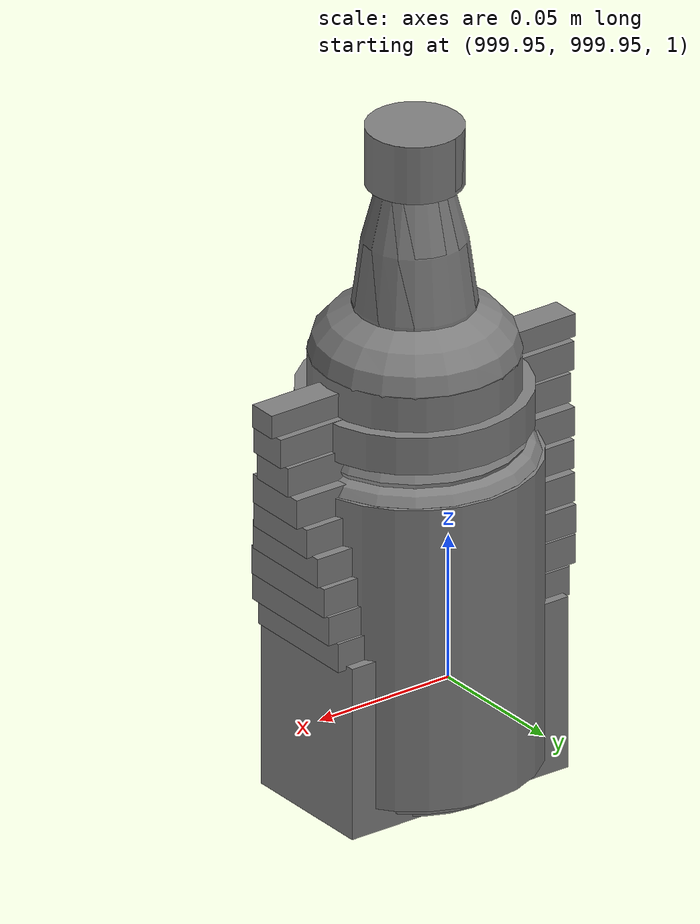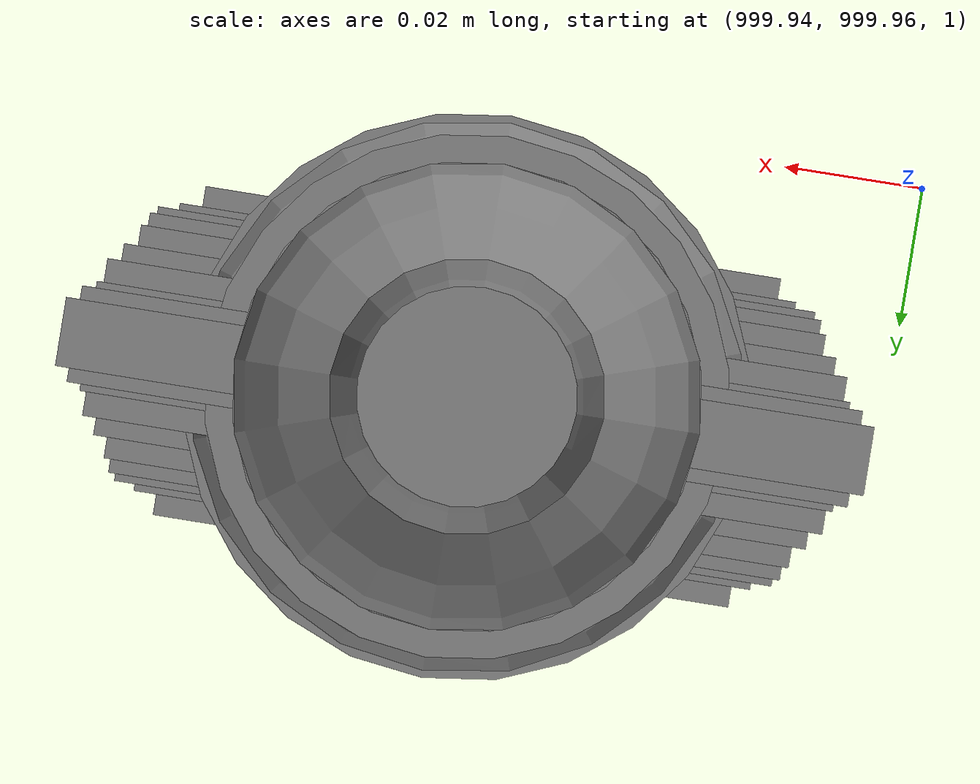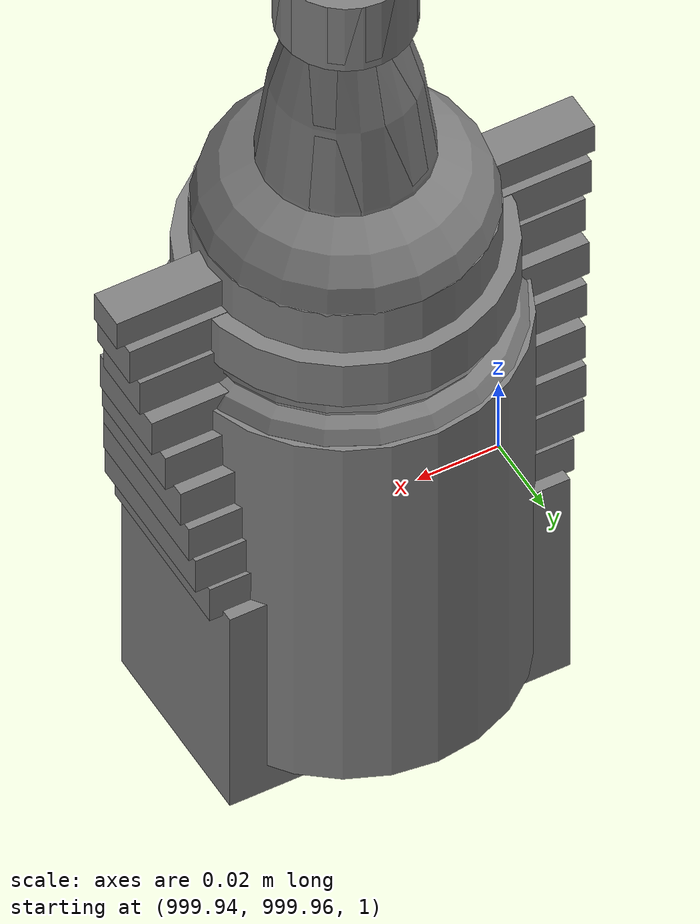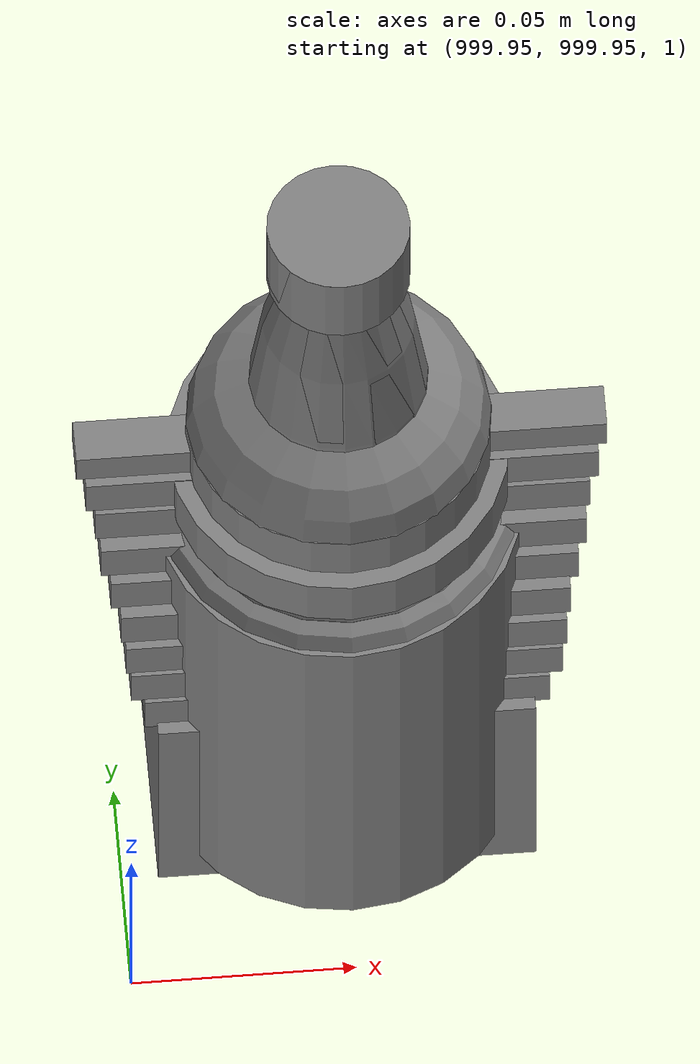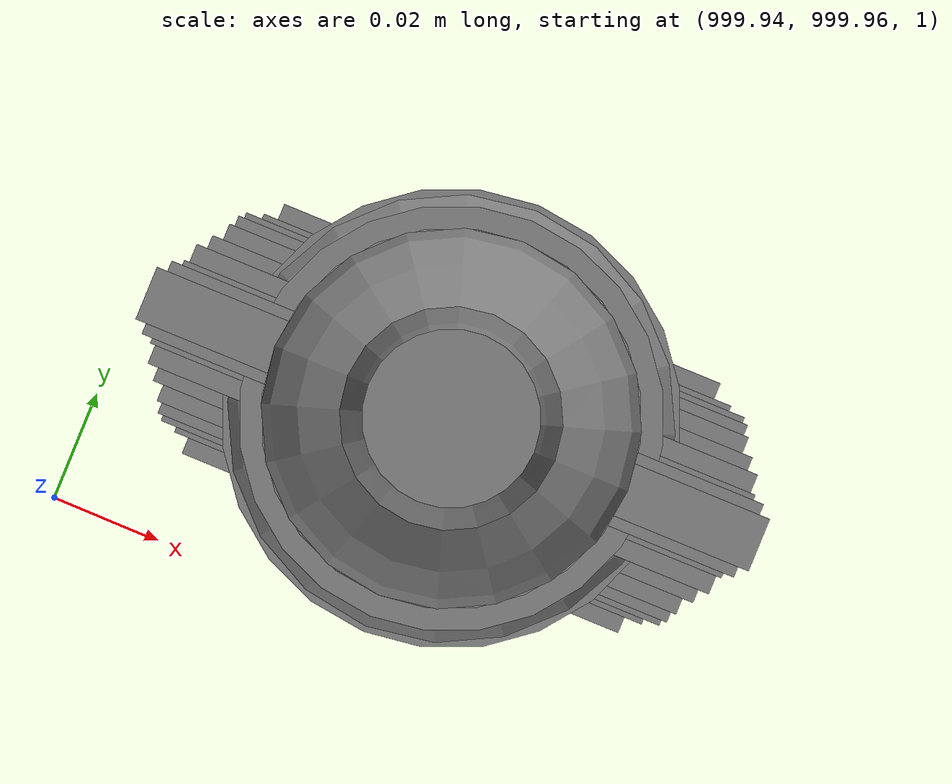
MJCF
<mujoco>
    <option gravity="0.000000000 0.000000000 -9.810000420" timestep="0.0166666" integrator="implicitfast" density="1.225" viscosity="1.8000001e-05" noslip_iterations="10" iterations="100" sdf_iterations="50">
        <flag multiccd="disable"/>
    </option>
    <size memory="1000M"/>
    <compiler coordinate="local"/>
    <worldbody>
        <light cutoff="30" pos="0 1 1" dir="0 -1 -2"/>
        <light cutoff="30" pos="0 -1 1" dir="0 1 -2"/>
        <body pos="0.000000000 0.000000000 0.000000000" euler="0.000000000 0.000000000 0.000000000" name="Interactive Objects_Interactive Objects"/>
        <body pos="1000.000000000 1000.000000000 1.000000000" euler="0.000000000 0.000000000 0.000000000" name="openloong_gripper_2f85_fix_base_usda_can">
            <geom contype="1" conaffinity="1" density="1000" type="cylinder" material="" rgba="0.500000000 0.500000000 0.500000000 1.000000000" solimp="0.899999976 0.949999988 0.001000000" friction="1.000000000 0.005000000 0.000100000" solref="0.020000000 1.000000000" margin="0" condim="3" group="0" pos="0.000000000 0.000000000 0.079676986" quat="1.000000000 0.000000000 0.000000000 0.000000000" size="0.034000002 0.071999997 1.000000000" name="openloong_gripper_2f85_fix_base_usda_geom_1DD582E0_443E_48B2_80F4_CDCD6FFCBB99"/>
            <geom contype="1" conaffinity="1" density="1000" type="ellipsoid" material="" rgba="0.500000000 0.500000000 0.500000000 1.000000000" solimp="0.899999976 0.949999988 0.001000000" friction="1.000000000 0.005000000 0.000100000" solref="0.020000000 1.000000000" margin="0" condim="3" group="0" pos="0.000000000 0.000000000 0.151854277" quat="1.000000000 0.000000000 0.000000000 0.000000000" size="0.034000002 0.034000002 0.020000000" name="openloong_gripper_2f85_fix_base_usda_geom_5F86948B_D4AF_47D1_92A9_1A780DEF45A1"/>
            <geom contype="1" conaffinity="1" density="1000" type="box" material="" rgba="0.500000000 0.500000000 0.500000000 1.000000000" solimp="0.899999976 0.949999988 0.001000000" friction="1.000000000 0.005000000 0.000100000" solref="0.020000000 1.000000000" margin="0" condim="3" group="0" pos="0.000000000 0.000000000 0.004777670" quat="1.000000000 0.000000000 0.000000000 0.000000000" size="0.020000000 0.020000000 0.005000000" name="openloong_gripper_2f85_fix_base_usda_geom_0879B162_D88E_468B_9396_5EF1A5FA2270"/>
            <freejoint name="openloong_gripper_2f85_fix_base_usda_can_joint"/>
            <site size="0.005000000 0.005000000 0.005000000" rgba="0.500000000 0.500000000 0.500000000 1.000000000" pos="0.000000000 0.000000000 0.000000000" quat="1.000000000 0.000000000 0.000000000 0.000000000" group="0" type="sphere" name="openloong_gripper_2f85_fix_base_usda_cansite"/>
        </body>
        <body pos="1000.000000000 1000.000000000 1.000000000" euler="0.000000000 0.000000000 0.000000000" name="openloong_gripper_2f85_fix_base_usda_bottle_red">
            <geom contype="1" conaffinity="1" density="1000" type="ellipsoid" material="" rgba="0.500000000 0.500000000 0.500000000 1.000000000" solimp="0.899999976 0.949999988 0.001000000" friction="1.000000000 0.005000000 0.000100000" solref="0.020000000 1.000000000" margin="0" condim="3" group="0" pos="0.000000000 0.000000000 0.144284487" quat="1.000000000 0.000000000 0.000000000 0.000000000" size="0.021000000 0.021000000 0.079999998" name="openloong_gripper_2f85_fix_base_usda_geom_9E6057A1_BA51_4EE4_B597_50CDA832533B"/>
            <geom contype="1" conaffinity="1" density="1000" type="cylinder" material="" rgba="0.500000000 0.500000000 0.500000000 1.000000000" solimp="0.899999976 0.949999988 0.001000000" friction="1.000000000 0.005000000 0.000100000" solref="0.020000000 1.000000000" margin="0" condim="3" group="0" pos="0.000000000 0.000000000 0.220618963" quat="1.000000000 0.000000000 0.000000000 0.000000000" size="0.016000001 0.010000000 1.000000000" name="openloong_gripper_2f85_fix_base_usda_geom_18DC17BB_8886_4C0B_B880_D9B173F2FD7A"/>
            <geom contype="1" conaffinity="1" density="1000" type="ellipsoid" material="" rgba="0.500000000 0.500000000 0.500000000 1.000000000" solimp="0.899999976 0.949999988 0.001000000" friction="1.000000000 0.005000000 0.000100000" solref="0.020000000 1.000000000" margin="0" condim="3" group="0" pos="0.000000000 0.000000000 0.118945479" quat="1.000000000 0.000000000 0.000000000 0.000000000" size="0.030999999 0.030999999 0.029999999" name="openloong_gripper_2f85_fix_base_usda_geom_509EADA3_8B4A_4498_898D_FAE6B77DB933"/>
            <geom contype="1" conaffinity="1" density="1000" type="box" material="" rgba="0.500000000 0.500000000 0.500000000 1.000000000" solimp="0.899999976 0.949999988 0.001000000" friction="1.000000000 0.005000000 0.000100000" solref="0.020000000 1.000000000" margin="0" condim="3" group="0" pos="0.000000000 0.000000000 0.002189159" quat="1.000000000 0.000000000 0.000000000 0.000000000" size="0.020000000 0.020000000 0.003000000" name="openloong_gripper_2f85_fix_base_usda_geom_2EF3833C_838D_4A8E_ACDD_AFF1ECAC447B"/>
            <geom contype="1" conaffinity="1" density="1000" type="cylinder" material="" rgba="0.500000000 0.500000000 0.500000000 1.000000000" solimp="0.899999976 0.949999988 0.001000000" friction="1.000000000 0.005000000 0.000100000" solref="0.020000000 1.000000000" margin="0" condim="3" group="0" pos="0.000000000 -0.000366211 0.060884237" quat="1.000000000 0.000000000 0.000000000 0.000000000" size="0.030999999 0.057999998 1.000000000" name="openloong_gripper_2f85_fix_base_usda_geom_2FEBD420_0267_4047_BB28_F7CB014D6420"/>
            <freejoint name="openloong_gripper_2f85_fix_base_usda_bottle_red_joint"/>
            <site size="0.005000000 0.005000000 0.005000000" rgba="0.500000000 0.500000000 0.500000000 1.000000000" pos="0.000000000 0.000000000 0.000000000" quat="0.999961913 0.008726535 0.000000000 0.000000000" group="0" type="sphere" name="openloong_gripper_2f85_fix_base_usda_bottle_redsite"/>
        </body>
        <body pos="-1.931404591 6.162186623 1.724914789" euler="-151.536346436 -25.455671310 15.742149353" mocap="true" name="spotlight6_SpotLight"/>
        <body pos="1000.000000000 1000.000000000 1.000000000" euler="0.000000000 0.000000000 0.000000000" name="openloong_gripper_2f85_fix_base_usda_bottle_blue">
            <geom contype="1" conaffinity="1" density="1000" type="ellipsoid" material="" rgba="0.500000000 0.500000000 0.500000000 1.000000000" solimp="0.899999976 0.949999988 0.001000000" friction="1.000000000 0.005000000 0.000100000" solref="0.020000000 1.000000000" margin="0" condim="3" group="0" pos="0.000000000 0.000000000 0.118920922" quat="1.000000000 0.000000000 0.000000000 0.000000000" size="0.030999999 0.030999999 0.029999999" name="openloong_gripper_2f85_fix_base_usda_geom_C47B1143_025A_4962_9F84_3F41F368ADB2"/>
            <geom contype="1" conaffinity="1" density="1000" type="box" material="" rgba="0.500000000 0.500000000 0.500000000 1.000000000" solimp="0.899999976 0.949999988 0.001000000" friction="1.000000000 0.005000000 0.000100000" solref="0.020000000 1.000000000" margin="0" condim="3" group="0" pos="0.000000000 0.000000000 0.002164602" quat="1.000000000 0.000000000 0.000000000 0.000000000" size="0.020000000 0.020000000 0.003000000" name="openloong_gripper_2f85_fix_base_usda_geom_6813FEEA_C66F_4F0B_BE81_D911A0E74D1C"/>
            <geom contype="1" conaffinity="1" density="1000" type="cylinder" material="" rgba="0.500000000 0.500000000 0.500000000 1.000000000" solimp="0.899999976 0.949999988 0.001000000" friction="1.000000000 0.005000000 0.000100000" solref="0.020000000 1.000000000" margin="0" condim="3" group="0" pos="0.000000000 -0.000366211 0.060859680" quat="1.000000000 0.000000000 0.000000000 0.000000000" size="0.030999999 0.057999998 1.000000000" name="openloong_gripper_2f85_fix_base_usda_geom_BFC1C53A_5EC0_4DE0_9C87_E526A14DB11D"/>
            <geom contype="1" conaffinity="1" density="1000" type="cylinder" material="" rgba="0.500000000 0.500000000 0.500000000 1.000000000" solimp="0.899999976 0.949999988 0.001000000" friction="1.000000000 0.005000000 0.000100000" solref="0.020000000 1.000000000" margin="0" condim="3" group="0" pos="0.000000000 0.000000000 0.220594406" quat="1.000000000 0.000000000 0.000000000 0.000000000" size="0.016000001 0.010000000 1.000000000" name="openloong_gripper_2f85_fix_base_usda_geom_D3589AF5_5E91_4297_A76F_885A98F9DDB5"/>
            <geom contype="1" conaffinity="1" density="1000" type="ellipsoid" material="" rgba="0.500000000 0.500000000 0.500000000 1.000000000" solimp="0.899999976 0.949999988 0.001000000" friction="1.000000000 0.005000000 0.000100000" solref="0.020000000 1.000000000" margin="0" condim="3" group="0" pos="0.000000000 0.000000000 0.144259930" quat="1.000000000 0.000000000 0.000000000 0.000000000" size="0.021000000 0.021000000 0.079999998" name="openloong_gripper_2f85_fix_base_usda_geom_BE5130FB_CFE4_4058_A086_51C5B3CF71D9"/>
            <freejoint name="openloong_gripper_2f85_fix_base_usda_bottle_blue_joint"/>
            <site size="0.005000000 0.005000000 0.005000000" rgba="0.500000000 0.500000000 0.500000000 1.000000000" pos="0.000000000 0.000000000 0.000000000" quat="0.999961913 0.008726535 0.000000000 0.000000000" group="0" type="sphere" name="openloong_gripper_2f85_fix_base_usda_bottle_bluesite"/>
        </body>
        <body pos="1000.000000000 1000.000000000 1.000000000" euler="0.000000000 0.000000000 0.000000000" name="openloong_gripper_2f85_fix_base_usda_salt">
            <geom contype="1" conaffinity="1" density="1000" type="box" material="" rgba="0.500000000 0.500000000 0.500000000 1.000000000" solimp="0.899999976 0.949999988 0.001000000" friction="1.000000000 0.005000000 0.000100000" solref="0.020000000 1.000000000" margin="0" condim="3" group="0" pos="0.000305176 0.000000000 0.084862232" quat="1.000000000 0.000000000 0.000000000 0.000000000" size="0.048999999 0.018999999 0.005000000" name="openloong_gripper_2f85_fix_base_usda_geom_08D0F45F_8AB1_4A0A_BE16_CC63EFABC5C7"/>
            <geom contype="1" conaffinity="1" density="1000" type="box" material="" rgba="0.500000000 0.500000000 0.500000000 1.000000000" solimp="0.899999976 0.949999988 0.001000000" friction="1.000000000 0.005000000 0.000100000" solref="0.020000000 1.000000000" margin="0" condim="3" group="0" pos="0.000305176 0.000000000 0.104564309" quat="1.000000000 0.000000000 0.000000000 0.000000000" size="0.052000001 0.014000000 0.005000000" name="openloong_gripper_2f85_fix_base_usda_geom_67AE841C_581C_4EBB_A0E0_E9C4ED21C2CC"/>
            <geom contype="1" conaffinity="1" density="1000" type="box" material="" rgba="0.500000000 0.500000000 0.500000000 1.000000000" solimp="0.899999976 0.949999988 0.001000000" friction="1.000000000 0.005000000 0.000100000" solref="0.020000000 1.000000000" margin="0" condim="3" group="0" pos="0.000305176 0.000000000 0.114487171" quat="1.000000000 0.000000000 0.000000000 0.000000000" size="0.054000001 0.011500000 0.005000000" name="openloong_gripper_2f85_fix_base_usda_geom_2646E8C0_A627_4CE4_8213_914D20D23E8C"/>
            <geom contype="1" conaffinity="1" density="1000" type="box" material="" rgba="0.500000000 0.500000000 0.500000000 1.000000000" solimp="0.899999976 0.949999988 0.001000000" friction="1.000000000 0.005000000 0.000100000" solref="0.020000000 1.000000000" margin="0" condim="3" group="0" pos="0.000305176 0.000000000 0.075103164" quat="1.000000000 0.000000000 0.000000000 0.000000000" size="0.048000000 0.020000000 0.005000000" name="openloong_gripper_2f85_fix_base_usda_geom_8069BBAA_157F_42A8_8650_A5672A2941E9"/>
            <geom contype="1" conaffinity="1" density="1000" type="box" material="" rgba="0.500000000 0.500000000 0.500000000 1.000000000" solimp="0.899999976 0.949999988 0.001000000" friction="1.000000000 0.005000000 0.000100000" solref="0.020000000 1.000000000" margin="0" condim="3" group="0" pos="0.000305176 0.000000000 0.134892464" quat="1.000000000 0.000000000 0.000000000 0.000000000" size="0.057000000 0.007000000 0.005000000" name="openloong_gripper_2f85_fix_base_usda_geom_7D365F97_9B52_48B6_A50E_1034ECB553E0"/>
            <geom contype="1" conaffinity="1" density="1000" type="box" material="" rgba="0.500000000 0.500000000 0.500000000 1.000000000" solimp="0.899999976 0.949999988 0.001000000" friction="1.000000000 0.005000000 0.000100000" solref="0.020000000 1.000000000" margin="0" condim="3" group="0" pos="0.000305176 0.000000000 0.094920278" quat="1.000000000 0.000000000 0.000000000 0.000000000" size="0.050000001 0.017000001 0.005000000" name="openloong_gripper_2f85_fix_base_usda_geom_645D45D7_3726_41B1_8D5D_083938A3AEFA"/>
            <geom contype="1" conaffinity="1" density="1000" type="box" material="" rgba="0.500000000 0.500000000 0.500000000 1.000000000" solimp="0.899999976 0.949999988 0.001000000" friction="1.000000000 0.005000000 0.000100000" solref="0.020000000 1.000000000" margin="0" condim="3" group="0" pos="0.000305176 0.000000000 0.065204859" quat="1.000000000 0.000000000 0.000000000 0.000000000" size="0.045000002 0.021000000 0.005000000" name="openloong_gripper_2f85_fix_base_usda_geom_C883C849_11DE_4051_B7B3_C63DB0BF6A54"/>
            <geom contype="1" conaffinity="1" density="1000" type="box" material="" rgba="0.500000000 0.500000000 0.500000000 1.000000000" solimp="0.899999976 0.949999988 0.001000000" friction="1.000000000 0.005000000 0.000100000" solref="0.020000000 1.000000000" margin="0" condim="3" group="0" pos="0.000305176 0.000000000 0.144135714" quat="1.000000000 0.000000000 0.000000000 0.000000000" size="0.059000000 0.005000000 0.004000000" name="openloong_gripper_2f85_fix_base_usda_geom_5785FEE2_1090_491D_B537_A5F363CD6BFF"/>
            <geom contype="1" conaffinity="1" density="1000" type="box" material="" rgba="0.500000000 0.500000000 0.500000000 1.000000000" solimp="0.899999976 0.949999988 0.001000000" friction="1.000000000 0.005000000 0.000100000" solref="0.020000000 1.000000000" margin="0" condim="3" group="0" pos="0.000000000 0.000000000 0.031593561" quat="1.000000000 0.000000000 0.000000000 0.000000000" size="0.041999999 0.024000000 0.029999999" name="openloong_gripper_2f85_fix_base_usda_geom_F0149E1A_95DF_4FAA_99E4_AAACE6A9A4E4"/>
            <geom contype="1" conaffinity="1" density="1000" type="box" material="" rgba="0.500000000 0.500000000 0.500000000 1.000000000" solimp="0.899999976 0.949999988 0.001000000" friction="1.000000000 0.005000000 0.000100000" solref="0.020000000 1.000000000" margin="0" condim="3" group="0" pos="0.000305176 0.000000000 0.124608755" quat="1.000000000 0.000000000 0.000000000 0.000000000" size="0.055000000 0.008000000 0.005000000" name="openloong_gripper_2f85_fix_base_usda_geom_8700707F_BCCE_44E5_A492_EA4F814969FF"/>
            <freejoint name="openloong_gripper_2f85_fix_base_usda_salt_joint"/>
            <site size="0.005000000 0.005000000 0.005000000" rgba="0.500000000 0.500000000 0.500000000 1.000000000" pos="0.000000000 0.000000000 0.000000000" quat="1.000000000 0.000000000 0.000000000 0.000000000" group="0" type="sphere" name="openloong_gripper_2f85_fix_base_usda_saltsite"/>
        </body>
        <body pos="-2.028046370 6.057257175 1.774178624" euler="-31.936676025 -78.826484680 3.825384378" mocap="true" name="spotlight5_SpotLight"/>
        <body pos="-2.096717834 6.120712280 1.744234443" euler="-64.279045105 61.635807037 -73.259597778" mocap="true" name="spotlight1_SpotLight"/>
        <body pos="1000.000000000 1000.000000000 1.000000000" euler="0.000000000 0.000000000 0.000000000" name="openloong_gripper_2f85_fix_base_usda_jar_01">
            <geom contype="1" conaffinity="1" density="1000" type="box" material="" rgba="0.500000000 0.500000000 0.500000000 1.000000000" solimp="0.899999976 0.949999988 0.001000000" friction="1.000000000 0.005000000 0.000100000" solref="0.020000000 1.000000000" margin="0" condim="3" group="0" pos="0.000000000 0.000000000 0.006158113" quat="1.000000000 0.000000000 0.000000000 0.000000000" size="0.020000000 0.020000000 0.005000000" name="openloong_gripper_2f85_fix_base_usda_geom_FCF1DE9A_D20A_4FEE_ABBD_0AD91AA8F16A"/>
            <geom contype="1" conaffinity="1" density="1000" type="cylinder" material="" rgba="0.500000000 0.500000000 0.500000000 1.000000000" solimp="0.899999976 0.949999988 0.001000000" friction="1.000000000 0.005000000 0.000100000" solref="0.020000000 1.000000000" margin="0" condim="3" group="0" pos="0.000000000 0.000000000 0.062744498" quat="1.000000000 0.000000000 0.000000000 0.000000000" size="0.041000001 0.052999999 1.000000000" name="openloong_gripper_2f85_fix_base_usda_geom_79481474_11E5_4783_A9E7_06053B0D7EE4"/>
            <geom contype="1" conaffinity="1" density="1000" type="ellipsoid" material="" rgba="0.500000000 0.500000000 0.500000000 1.000000000" solimp="0.899999976 0.949999988 0.001000000" friction="1.000000000 0.005000000 0.000100000" solref="0.020000000 1.000000000" margin="0" condim="3" group="0" pos="0.000000000 0.000000000 0.122252703" quat="1.000000000 0.000000000 0.000000000 0.000000000" size="0.035999998 0.035999998 0.010000000" name="openloong_gripper_2f85_fix_base_usda_geom_0F0DE520_69A1_4A26_9412_94957E53516A"/>
            <geom contype="1" conaffinity="1" density="1000" type="cylinder" material="" rgba="0.500000000 0.500000000 0.500000000 1.000000000" solimp="0.899999976 0.949999988 0.001000000" friction="1.000000000 0.005000000 0.000100000" solref="0.020000000 1.000000000" margin="0" condim="3" group="0" pos="0.000000000 0.000000000 0.015747190" quat="1.000000000 0.000000000 0.000000000 0.000000000" size="0.035000000 0.010000000 1.000000000" name="openloong_gripper_2f85_fix_base_usda_geom_5C09AA5E_4220_4341_8E7A_89D1E6DD152B"/>
            <geom contype="1" conaffinity="1" density="1000" type="ellipsoid" material="" rgba="0.500000000 0.500000000 0.500000000 1.000000000" solimp="0.899999976 0.949999988 0.001000000" friction="1.000000000 0.005000000 0.000100000" solref="0.020000000 1.000000000" margin="0" condim="3" group="0" pos="0.000000000 0.000000000 0.115815401" quat="1.000000000 0.000000000 0.000000000 0.000000000" size="0.039999999 0.039999999 0.010000000" name="openloong_gripper_2f85_fix_base_usda_geom_4A1F3E34_2725_4118_83A7_EFE202D14AF3"/>
            <geom contype="1" conaffinity="1" density="1000" type="cylinder" material="" rgba="0.500000000 0.500000000 0.500000000 1.000000000" solimp="0.899999976 0.949999988 0.001000000" friction="1.000000000 0.005000000 0.000100000" solref="0.020000000 1.000000000" margin="0" condim="3" group="0" pos="0.000000000 0.000000000 0.133183479" quat="1.000000000 0.000000000 0.000000000 0.000000000" size="0.037999999 0.006500000 1.000000000" name="openloong_gripper_2f85_fix_base_usda_geom_929E7377_7729_41DC_BB31_99AD1FE6CFDA"/>
            <freejoint name="openloong_gripper_2f85_fix_base_usda_jar_01_joint"/>
            <site size="0.005000000 0.005000000 0.005000000" rgba="0.500000000 0.500000000 0.500000000 1.000000000" pos="0.000000000 0.000000000 0.000000000" quat="1.000000000 0.000000000 0.000000000 0.000000000" group="0" type="sphere" name="openloong_gripper_2f85_fix_base_usda_jar_01site"/>
        </body>
        <body pos="0.000000000 0.000000000 0.000000000" euler="0.000000000 0.000000000 0.000000000" name=" Static Objects_ Static Objects">
            <geom contype="1" conaffinity="1" density="1000" type="box" material="" rgba="0.500000000 0.500000000 0.500000000 1.000000000" solimp="0.899999976 0.949999988 0.001000000" friction="1.000000000 0.005000000 0.000100000" solref="0.020000000 1.000000000" margin="0" condim="3" group="0" pos="-6.286010742 6.153595448 1.563861728" quat="0.707107067 0.000000000 0.000000000 0.707106471" size="0.529999971 3.134999990 0.025000000" name=" Static Objects_geom_570F4CBB_CE2D_4C28_835D_C9E8BC049BA7"/>
            <geom contype="1" conaffinity="1" density="1000" type="box" material="" rgba="0.500000000 0.500000000 0.500000000 1.000000000" solimp="0.899999976 0.949999988 0.001000000" friction="1.000000000 0.005000000 0.000100000" solref="0.020000000 1.000000000" margin="0" condim="3" group="0" pos="-3.101639986 6.150595188 1.018643856" quat="1.000000000 0.000000000 0.000000000 0.000000000" size="0.050000001 0.579999983 1.019999981" name=" Static Objects_geom_9A0D7C22_B238_4F02_9EE3_5699B13C1BBB"/>
            <geom contype="1" conaffinity="1" density="1000" type="box" material="" rgba="0.500000000 0.500000000 0.500000000 1.000000000" solimp="0.899999976 0.949999988 0.001000000" friction="1.000000000 0.005000000 0.000100000" solref="0.020000000 1.000000000" margin="0" condim="3" group="0" pos="-2.825197220 6.153595448 1.563861728" quat="0.707107067 0.000000000 0.000000000 0.707106471" size="0.550000012 0.239999995 0.025000000" name=" Static Objects_geom_65616F1A_DF3D_4C7A_AE84_98B7E90F1AAE"/>
            <geom contype="1" conaffinity="1" density="1000" type="box" material="" rgba="0.500000000 0.500000000 0.500000000 1.000000000" solimp="0.899999976 0.949999988 0.001000000" friction="1.000000000 0.005000000 0.000100000" solref="0.020000000 1.000000000" margin="0" condim="3" group="0" pos="-6.311686516 6.153595448 1.018643856" quat="0.707107067 0.000000000 0.000000000 0.707106471" size="0.050000001 3.150000095 1.019999981" name=" Static Objects_geom_7E395631_4879_461B_AE38_447F7A395AE4"/>
            <geom contype="1" conaffinity="1" density="1000" type="box" material="" rgba="0.500000000 0.500000000 0.500000000 1.000000000" solimp="0.899999976 0.949999988 0.001000000" friction="1.000000000 0.005000000 0.000100000" solref="0.020000000 1.000000000" margin="0" condim="3" group="0" pos="-2.825197220 6.153595448 1.115278244" quat="0.707107067 0.000000000 0.000000000 0.707106471" size="0.550000012 0.239999995 0.025000000" name=" Static Objects_geom_E9317C3F_F744_442F_931A_C635972F54D9"/>
            <geom contype="1" conaffinity="1" density="1000" type="box" material="" rgba="0.500000000 0.500000000 0.500000000 1.000000000" solimp="0.899999976 0.949999988 0.001000000" friction="1.000000000 0.005000000 0.000100000" solref="0.020000000 1.000000000" margin="0" condim="3" group="0" pos="-6.293097973 6.153595448 1.114443064" quat="0.707107067 0.000000000 0.000000000 0.707106471" size="0.529999971 3.134999990 0.025000000" name=" Static Objects_geom_847E73FB_5503_4E1D_9646_1FACE4F79079"/>
            <geom contype="1" conaffinity="1" density="1000" type="box" material="" rgba="0.500000000 0.500000000 0.500000000 1.000000000" solimp="0.899999976 0.949999988 0.001000000" friction="1.000000000 0.005000000 0.000100000" solref="0.020000000 1.000000000" margin="0" condim="3" group="0" pos="-2.825197220 6.153595448 0.629031777" quat="0.707107067 0.000000000 0.000000000 0.707106471" size="0.550000012 0.239999995 0.025000000" name=" Static Objects_geom_4C8148AF_DCE3_455D_9181_4BD8C7886ECC"/>
            <geom contype="1" conaffinity="1" density="1000" type="box" material="" rgba="0.500000000 0.500000000 0.500000000 1.000000000" solimp="0.899999976 0.949999988 0.001000000" friction="1.000000000 0.005000000 0.000100000" solref="0.020000000 1.000000000" margin="0" condim="3" group="0" pos="-6.286010742 6.153595448 0.096129179" quat="0.707107067 0.000000000 0.000000000 0.707106471" size="0.529999971 3.134999990 0.098999999" name=" Static Objects_geom_76962240_0E16_4988_93CB_967377585095"/>
            <geom contype="1" conaffinity="1" density="1000" type="box" material="" rgba="0.500000000 0.500000000 0.500000000 1.000000000" solimp="0.899999976 0.949999988 0.001000000" friction="1.000000000 0.005000000 0.000100000" solref="0.020000000 1.000000000" margin="0" condim="3" group="0" pos="-2.825197220 6.153595448 0.097434282" quat="0.707107067 0.000000000 0.000000000 0.707106471" size="0.550000012 0.239999995 0.098999999" name=" Static Objects_geom_29111E12_E342_4596_A868_9EFBDC93756A"/>
            <geom contype="1" conaffinity="1" density="1000" type="box" material="" rgba="0.500000000 0.500000000 0.500000000 1.000000000" solimp="0.899999976 0.949999988 0.001000000" friction="1.000000000 0.005000000 0.000100000" solref="0.020000000 1.000000000" margin="0" condim="3" group="0" pos="-6.286010742 6.153595448 0.629031777" quat="0.707107067 0.000000000 0.000000000 0.707106471" size="0.529999971 3.134999990 0.025000000" name=" Static Objects_geom_D4361A64_03B4_426F_BDD8_E90CC63A6183"/>
            <geom contype="1" conaffinity="1" density="1000" type="box" material="" rgba="0.500000000 0.500000000 0.500000000 1.000000000" solimp="0.899999976 0.949999988 0.001000000" friction="1.000000000 0.005000000 0.000100000" solref="0.020000000 1.000000000" margin="0" condim="3" group="0" pos="-6.000000000 20.159999847 2.000000000" quat="1.000000000 0.000000000 0.000000000 0.000000000" size="6.079999924 0.070000000 2.000000000" name=" Static Objects_geom_21A21220_7C97_439C_B3A7_516C8BD81972"/>
            <geom contype="1" conaffinity="1" density="1000" type="box" material="" rgba="0.500000000 0.500000000 0.500000000 1.000000000" solimp="0.899999976 0.949999988 0.001000000" friction="1.000000000 0.005000000 0.000100000" solref="0.020000000 1.000000000" margin="0" condim="3" group="0" pos="-6.000000000 0.035000000 2.000000000" quat="1.000000000 0.000000000 0.000000000 0.000000000" size="6.079999924 0.070000000 2.000000000" name=" Static Objects_geom_7FCECB36_A440_4370_8A64_8A4E156FFE58"/>
            <geom contype="1" conaffinity="1" density="1000" type="box" material="" rgba="0.500000000 0.500000000 0.500000000 1.000000000" solimp="0.899999976 0.949999988 0.001000000" friction="1.000000000 0.005000000 0.000100000" solref="0.020000000 1.000000000" margin="0" condim="3" group="0" pos="0.000000000 10.000000000 2.000000000" quat="1.000000000 0.000000000 0.000000000 0.000000000" size="0.070000000 10.500000000 2.000000000" name=" Static Objects_geom_912EAE07_B863_4C0E_B21B_3EA6177B088A"/>
            <geom contype="1" conaffinity="1" density="1000" type="box" material="" rgba="0.500000000 0.500000000 0.500000000 1.000000000" solimp="0.899999976 0.949999988 0.001000000" friction="1.000000000 0.005000000 0.000100000" solref="0.020000000 1.000000000" margin="0" condim="3" group="0" pos="-12.050000191 10.000000000 2.000000000" quat="1.000000000 0.000000000 0.000000000 0.000000000" size="0.070000000 10.500000000 2.000000000" name=" Static Objects_geom_A8C93C2E_BCB4_4F57_802C_2FB554261F0A"/>
            <geom contype="1" conaffinity="1" density="1000" type="plane" material="" rgba="0.500000000 0.500000000 0.500000000 1.000000000" solimp="0.899999976 0.949999988 0.001000000" friction="1.000000000 0.005000000 0.000100000" solref="0.020000000 1.000000000" margin="0" condim="3" group="0" pos="-6.000000000 10.399999619 0.000000000" quat="1.000000000 0.000000000 0.000000000 0.000000000" size="6.050000191 10.800000191 0.010000000" name=" Static Objects_geom_DBC05480_AE0B_4F97_BACB_A5FB3A98985C"/>
            <geom contype="1" conaffinity="1" density="1000" type="box" material="" rgba="0.500000000 0.500000000 0.500000000 1.000000000" solimp="0.899999976 0.949999988 0.001000000" friction="1.000000000 0.005000000 0.000100000" solref="0.020000000 1.000000000" margin="0" condim="3" group="0" pos="-8.830721855 2.096410990 0.549305558" quat="1.000000000 0.000000000 0.000000000 0.000000000" size="0.280000001 0.430000007 0.550000012" name=" Static Objects_geom_EBB282BD_6139_45C7_BF9B_234728EFD310"/>
            <geom contype="1" conaffinity="1" density="1000" type="box" material="" rgba="0.500000000 0.500000000 0.500000000 1.000000000" solimp="0.899999976 0.949999988 0.001000000" friction="1.000000000 0.005000000 0.000100000" solref="0.020000000 1.000000000" margin="0" condim="3" group="0" pos="-6.460197449 2.937205315 0.548931718" quat="1.000000000 0.000000000 0.000000000 0.000000000" size="2.650000095 0.430000007 0.550000012" name=" Static Objects_geom_C0288641_2BC5_4CB4_9275_FD26AE52AD1F"/>
            <geom contype="1" conaffinity="1" density="1000" type="box" material="" rgba="0.500000000 0.500000000 0.500000000 1.000000000" solimp="0.899999976 0.949999988 0.001000000" friction="1.000000000 0.005000000 0.000100000" solref="0.020000000 1.000000000" margin="0" condim="3" group="0" pos="-4.240264893 1.327049494 0.549888909" quat="1.000000000 0.000000000 0.000000000 0.000000000" size="0.430000007 1.200000048 0.550000012" name=" Static Objects_geom_B61FC2DB_3EB3_4FD4_8D88_399B1A8CD4AE"/>
            <geom contype="1" conaffinity="1" density="1000" type="box" material="" rgba="0.500000000 0.500000000 0.500000000 1.000000000" solimp="0.899999976 0.949999988 0.001000000" friction="1.000000000 0.005000000 0.000100000" solref="0.020000000 1.000000000" margin="0" condim="3" group="0" pos="-7.408766270 3.088089943 1.776644945" quat="0.928051054 0.000000000 0.000000000 0.372453064" size="0.050000001 0.100000001 0.050000001" name=" Static Objects_geom_49DDD2D7_BEF3_439D_8717_397E7A81F735"/>
            <geom contype="1" conaffinity="1" density="1000" type="box" material="" rgba="0.500000000 0.500000000 0.500000000 1.000000000" solimp="0.899999976 0.949999988 0.001000000" friction="1.000000000 0.005000000 0.000100000" solref="0.020000000 1.000000000" margin="0" condim="3" group="0" pos="-7.437745571 3.067511320 1.289965630" quat="1.000000000 0.000000000 0.000000000 0.000000000" size="0.029999999 0.020000000 0.020000000" name=" Static Objects_geom_D26260EF_8D81_48E4_B33F_298BEF9CC691"/>
            <geom contype="1" conaffinity="1" density="1000" type="box" material="" rgba="0.500000000 0.500000000 0.500000000 1.000000000" solimp="0.899999976 0.949999988 0.001000000" friction="1.000000000 0.005000000 0.000100000" solref="0.020000000 1.000000000" margin="0" condim="3" group="0" pos="-7.719123363 2.867671013 1.173410416" quat="1.000000000 0.000000000 0.000000000 0.000000000" size="0.250000000 0.250000000 0.079999998" name=" Static Objects_geom_55320EB5_98BF_4404_8443_040476E09451"/>
            <geom contype="1" conaffinity="1" density="1000" type="box" material="" rgba="0.500000000 0.500000000 0.500000000 1.000000000" solimp="0.899999976 0.949999988 0.001000000" friction="1.000000000 0.005000000 0.000100000" solref="0.020000000 1.000000000" margin="0" condim="3" group="0" pos="-7.719123363 2.958004713 1.530241251" quat="1.000000000 0.000000000 0.000000000 0.000000000" size="0.250000000 0.159999996 0.280000001" name=" Static Objects_geom_03C26EB0_6B93_404F_AAE2_8FC3995C3FD0"/>
            <geom contype="1" conaffinity="1" density="1000" type="cylinder" material="" rgba="0.500000000 0.500000000 0.500000000 1.000000000" solimp="0.899999976 0.949999988 0.001000000" friction="1.000000000 0.005000000 0.000100000" solref="0.020000000 1.000000000" margin="0" condim="3" group="0" pos="-7.427312374 3.069516420 1.502544641" quat="0.928051054 0.000000000 0.000000000 0.372453064" size="0.015000000 0.230000004 0.100000001" name=" Static Objects_geom_D50E39AF_A574_42DB_B8B5_64545E27CFF4"/>
            <geom contype="1" conaffinity="1" density="1000" type="box" material="" rgba="0.500000000 0.500000000 0.500000000 1.000000000" solimp="0.899999976 0.949999988 0.001000000" friction="1.000000000 0.005000000 0.000100000" solref="0.020000000 1.000000000" margin="0" condim="3" group="0" pos="-9.058088303 6.434794426 1.209077358" quat="1.000000000 0.000000000 0.000000000 0.000000000" size="0.250000000 0.100000001 0.070000000" name=" Static Objects_geom_187903CE_4576_4A97_9691_5AB73CF7EBB7"/>
            <geom contype="1" conaffinity="1" density="1000" type="box" material="" rgba="0.500000000 0.500000000 0.500000000 1.000000000" solimp="0.899999976 0.949999988 0.001000000" friction="1.000000000 0.005000000 0.000100000" solref="0.020000000 1.000000000" margin="0" condim="3" group="0" pos="-5.611940861 6.318420410 0.350975692" quat="1.000000000 0.000000000 0.000000000 0.000000000" size="0.699999988 0.100000001 0.150000006" name=" Static Objects_geom_16495B2F_9A08_4AB9_BBAA_E7D82840CF6F"/>
            <geom contype="1" conaffinity="1" density="1000" type="box" material="" rgba="0.500000000 0.500000000 0.500000000 1.000000000" solimp="0.899999976 0.949999988 0.001000000" friction="1.000000000 0.005000000 0.000100000" solref="0.020000000 1.000000000" margin="0" condim="3" group="0" pos="-9.237723351 6.464855671 1.209077358" quat="1.000000000 0.000000000 0.000000000 0.000000000" size="0.100000001 0.100000001 0.070000000" name=" Static Objects_geom_DF9B5298_30D3_4BC9_9CE6_A16CF62B3A76"/>
            <geom contype="1" conaffinity="1" density="1000" type="box" material="" rgba="0.500000000 0.500000000 0.500000000 1.000000000" solimp="0.899999976 0.949999988 0.001000000" friction="1.000000000 0.005000000 0.000100000" solref="0.020000000 1.000000000" margin="0" condim="3" group="0" pos="-6.300771236 6.459744930 1.744376063" quat="1.000000000 0.000000000 0.000000000 0.000000000" size="3.000000000 0.200000003 0.150000006" name=" Static Objects_geom_10952D6D_412C_4C3A_A083_1F8390708327"/>
            <geom contype="1" conaffinity="1" density="1000" type="box" material="" rgba="0.500000000 0.500000000 0.500000000 1.000000000" solimp="0.899999976 0.949999988 0.001000000" friction="1.000000000 0.005000000 0.000100000" solref="0.020000000 1.000000000" margin="0" condim="3" group="0" pos="-7.373087406 6.458900928 1.214329123" quat="1.000000000 0.000000000 0.000000000 0.000000000" size="0.250000000 0.200000003 0.075000003" name=" Static Objects_geom_BC57E852_5B25_4525_8EA5_DD4EBA9AF2CB"/>
            <geom contype="1" conaffinity="1" density="1000" type="box" material="" rgba="0.500000000 0.500000000 0.500000000 1.000000000" solimp="0.899999976 0.949999988 0.001000000" friction="1.000000000 0.005000000 0.000100000" solref="0.020000000 1.000000000" margin="0" condim="3" group="0" pos="-4.035642624 6.459744930 0.352518857" quat="1.000000000 0.000000000 0.000000000 0.000000000" size="0.800000012 0.200000003 0.150000006" name=" Static Objects_geom_042702D1_24C8_4B12_BA61_6528BA941443"/>
            <geom contype="1" conaffinity="1" density="1000" type="box" material="" rgba="0.500000000 0.500000000 0.500000000 1.000000000" solimp="0.899999976 0.949999988 0.001000000" friction="1.000000000 0.005000000 0.000100000" solref="0.020000000 1.000000000" margin="0" condim="3" group="0" pos="-3.907610416 6.318625927 0.800981164" quat="1.000000000 0.000000000 0.000000000 0.000000000" size="0.500000000 0.100000001 0.150000006" name=" Static Objects_geom_F51E361E_CF1B_49AC_883D_84FB3026F990"/>
            <geom contype="1" conaffinity="1" density="1000" type="box" material="" rgba="0.500000000 0.500000000 0.500000000 1.000000000" solimp="0.899999976 0.949999988 0.001000000" friction="1.000000000 0.005000000 0.000100000" solref="0.020000000 1.000000000" margin="0" condim="3" group="0" pos="-6.098561764 6.327973843 1.292199373" quat="1.000000000 0.000000000 0.000000000 0.000000000" size="0.500000000 0.100000001 0.150000006" name=" Static Objects_geom_0BF01138_81D4_45C0_A0D3_F980DD57373C"/>
            <geom contype="1" conaffinity="1" density="1000" type="box" material="" rgba="0.500000000 0.500000000 0.500000000 1.000000000" solimp="0.899999976 0.949999988 0.001000000" friction="1.000000000 0.005000000 0.000100000" solref="0.020000000 1.000000000" margin="0" condim="3" group="0" pos="-7.886891365 6.459744930 0.352518857" quat="1.000000000 0.000000000 0.000000000 0.000000000" size="1.500000000 0.200000003 0.150000006" name=" Static Objects_geom_F0DCDD90_8F3A_4EE3_8B20_8EDD6287F378"/>
            <geom contype="1" conaffinity="1" density="1000" type="box" material="" rgba="0.500000000 0.500000000 0.500000000 1.000000000" solimp="0.899999976 0.949999988 0.001000000" friction="1.000000000 0.005000000 0.000100000" solref="0.020000000 1.000000000" margin="0" condim="3" group="0" pos="-6.824534416 6.447464466 1.212718010" quat="1.000000000 0.000000000 0.000000000 0.000000000" size="0.100000001 0.100000001 0.075000003" name=" Static Objects_geom_F3249C19_C3C5_4FE9_A251_ED55F504B29C"/>
            <geom contype="1" conaffinity="1" density="1000" type="box" material="" rgba="0.500000000 0.500000000 0.500000000 1.000000000" solimp="0.899999976 0.949999988 0.001000000" friction="1.000000000 0.005000000 0.000100000" solref="0.020000000 1.000000000" margin="0" condim="3" group="0" pos="-4.407354832 6.459744930 1.292199373" quat="1.000000000 0.000000000 0.000000000 0.000000000" size="1.240000010 0.200000003 0.150000006" name=" Static Objects_geom_E8D73AB4_A078_45DD_BAF1_DE933648C92B"/>
            <geom contype="1" conaffinity="1" density="1000" type="box" material="" rgba="0.500000000 0.500000000 0.500000000 1.000000000" solimp="0.899999976 0.949999988 0.001000000" friction="1.000000000 0.005000000 0.000100000" solref="0.020000000 1.000000000" margin="0" condim="3" group="0" pos="-6.751636982 6.459744930 0.800981164" quat="1.000000000 0.000000000 0.000000000 0.000000000" size="2.200000048 0.200000003 0.150000006" name=" Static Objects_geom_A7384EDA_8C5D_4F18_A8B7_759B9E94347B"/>
            <geom contype="1" conaffinity="1" density="1000" type="box" material="" rgba="0.500000000 0.500000000 0.500000000 1.000000000" solimp="0.899999976 0.949999988 0.001000000" friction="1.000000000 0.005000000 0.000100000" solref="0.020000000 1.000000000" margin="0" condim="3" group="0" pos="-6.924745083 6.362090111 1.214329123" quat="1.000000000 0.000000000 0.000000000 0.000000000" size="0.200000003 0.100000001 0.075000003" name=" Static Objects_geom_8C97FC8F_F12B_43FE_8B31_87D84AEB634D"/>
            <geom contype="1" conaffinity="1" density="1000" type="box" material="" rgba="0.500000000 0.500000000 0.500000000 1.000000000" solimp="0.899999976 0.949999988 0.001000000" friction="1.000000000 0.005000000 0.000100000" solref="0.020000000 1.000000000" margin="0" condim="3" group="0" pos="-8.844120979 6.464855671 1.209077358" quat="1.000000000 0.000000000 0.000000000 0.000000000" size="0.100000001 0.100000001 0.070000000" name=" Static Objects_geom_A612779F_A9AC_42DD_B5A5_6C21F7785980"/>
            <geom contype="1" conaffinity="1" density="1000" type="box" material="" rgba="0.500000000 0.500000000 0.500000000 1.000000000" solimp="0.899999976 0.949999988 0.001000000" friction="1.000000000 0.005000000 0.000100000" solref="0.020000000 1.000000000" margin="0" condim="3" group="0" pos="-3.157672644 6.136868477 1.348373055" quat="1.000000000 0.000000000 0.000000000 0.000000000" size="0.200000003 0.519999981 0.300000012" name=" Static Objects_geom_F6A13A96_712C_4035_A388_F27228CD3535"/>
        </body>
        <body pos="-6.332345009 2.779978037 1.034067392" euler="0.000000000 0.000000000 0.000000000" name="openloong_gripper_2f85_fix_base_usda_basket">
            <geom contype="1" conaffinity="1" density="100000" type="box" material="" rgba="0.500000000 0.500000000 0.500000000 1.000000000" solimp="0.899999976 0.949999988 0.001000000" friction="1.000000000 0.899999976 0.000100000" solref="0.020000000 1.000000000" margin="0" condim="3" group="0" pos="-0.039724827 -0.188568115 0.167089701" quat="0.997537494 0.070135131 0.000000000 0.000000000" size="0.150000006 0.006000000 0.108000003" name="openloong_gripper_2f85_fix_base_usda_geom_8641FC23_A60D_4B82_8293_C29513D8DE3B"/>
            <geom contype="1" conaffinity="1" density="100000" type="box" material="" rgba="0.500000000 0.500000000 0.500000000 1.000000000" solimp="0.899999976 0.949999988 0.001000000" friction="1.000000000 0.899999976 0.000100000" solref="0.020000000 1.000000000" margin="0" condim="3" group="0" pos="0.094372749 0.000000000 0.168361664" quat="0.706172049 0.036353335 0.036353379 0.706171215" size="0.200000003 0.006000000 0.108000003" name="openloong_gripper_2f85_fix_base_usda_geom_BBB32976_D3E1_4885_BE08_0FADDB503AE8"/>
            <geom contype="1" conaffinity="1" density="100000" type="box" material="" rgba="0.500000000 0.500000000 0.500000000 1.000000000" solimp="0.899999976 0.949999988 0.001000000" friction="1.000000000 0.899999976 0.000100000" solref="0.020000000 1.000000000" margin="0" condim="3" group="0" pos="-0.039724827 0.000000000 0.068126202" quat="1.000000000 0.000000000 0.000000000 0.000000000" size="0.129999995 0.174999997 0.006000000" name="openloong_gripper_2f85_fix_base_usda_geom_7F17ACA2_4E5A_48AD_8F88_3187ADCE6C91"/>
            <geom contype="1" conaffinity="1" density="100000" type="box" material="" rgba="0.500000000 0.500000000 0.500000000 1.000000000" solimp="0.899999976 0.949999988 0.001000000" friction="1.000000000 0.899999976 0.000100000" solref="0.020000000 1.000000000" margin="0" condim="3" group="0" pos="-0.039724827 0.188377380 0.167089701" quat="0.997489929 -0.070808925 0.000000000 0.000000000" size="0.150000006 0.006000000 0.108000003" name="openloong_gripper_2f85_fix_base_usda_geom_253BF800_2D88_420D_AA2E_A5B1C33C495C"/>
            <geom contype="1" conaffinity="1" density="100000" type="box" material="" rgba="0.500000000 0.500000000 0.500000000 1.000000000" solimp="0.899999976 0.949999988 0.001000000" friction="1.000000000 0.899999976 0.000100000" solref="0.020000000 1.000000000" margin="0" condim="3" group="0" pos="-0.172339439 0.000000000 0.168361664" quat="0.706172407 -0.036353018 -0.036353093 0.706170976" size="0.200000003 0.006000000 0.108000003" name="openloong_gripper_2f85_fix_base_usda_geom_7D40CEB9_8BD7_423F_B816_8A750C54FB51"/>
            <freejoint name="openloong_gripper_2f85_fix_base_usda_basket_joint"/>
            <site size="0.005000000 0.005000000 0.005000000" rgba="0.500000000 0.500000000 0.500000000 1.000000000" pos="0.000000000 0.000000000 0.000000000" quat="1.000000000 0.000000000 0.000000000 0.000000000" group="0" type="sphere" name="openloong_gripper_2f85_fix_base_usda_basketsite"/>
        </body>
        <body pos="-3.510578632 3.403555870 -0.000000100" euler="0.000000000 0.000000000 40.200675964" name="openloong_gripper_2f85_fix_base_usda_PZ">
            <geom contype="1" conaffinity="1" density="1000" type="box" material="" rgba="0.500000000 0.500000000 0.500000000 1.000000000" solimp="0.899999976 0.949999988 0.001000000" friction="1.000000000 0.005000000 0.000100000" solref="0.020000000 1.000000000" margin="0" condim="3" group="0" pos="-0.047453165 0.056484699 0.373715430" quat="0.934750080 0.077914521 0.028795123 0.345459938" size="0.180000007 0.010000000 0.379999995" name="openloong_gripper_2f85_fix_base_usda_geom_4874B216_A72F_4A2D_8164_D9CB34F7AE63"/>
            <geom contype="1" conaffinity="1" density="1000" type="box" material="" rgba="0.500000000 0.500000000 0.500000000 1.000000000" solimp="0.899999976 0.949999988 0.001000000" friction="1.000000000 0.005000000 0.000100000" solref="0.020000000 1.000000000" margin="0" condim="3" group="0" pos="0.047452450 -0.054376602 0.374072611" quat="0.934387863 -0.082143910 -0.030358355 0.345326364" size="0.180000007 0.010000000 0.379999995" name="openloong_gripper_2f85_fix_base_usda_geom_3E73F33A_F18B_419C_A9E7_D2F9C4CA6AF6"/>
            <freejoint name="openloong_gripper_2f85_fix_base_usda_PZ"/>
        </body>
        <body pos="-7.168000221 2.823999882 1.227496982" euler="-0.283413976 0.056829724 -0.133293271" name="openloong_gripper_2f85_fix_base_usda_Pos">
            <geom contype="1" conaffinity="1" density="1000" type="box" material="" rgba="0.500000000 0.500000000 0.500000000 1.000000000" solimp="0.899999976 0.949999988 0.001000000" friction="1.000000000 0.005000000 0.000100000" solref="0.020000000 1.000000000" margin="0" condim="3" group="0" pos="-0.002278805 0.074524641 -0.004134059" quat="0.315989345 0.948763072 -0.000000000 0.000000000" size="0.059999999 0.013000000 0.035000000" name="openloong_gripper_2f85_fix_base_usda_geom_9D504AF9_8141_403D_8E7B_F4B7ACF1135B"/>
            <geom contype="1" conaffinity="1" density="1000" type="box" material="" rgba="0.500000000 0.500000000 0.500000000 1.000000000" solimp="0.899999976 0.949999988 0.001000000" friction="1.000000000 0.005000000 0.000100000" solref="0.020000000 1.000000000" margin="0" condim="3" group="0" pos="-0.002278805 0.078031301 0.008128285" quat="0.990447521 -0.137893379 -0.000000000 -0.000000000" size="0.059999999 0.010000000 0.035000000" name="openloong_gripper_2f85_fix_base_usda_geom_3CEFED2E_808A_452D_99C6_6B0DC7917038"/>
            <geom contype="1" conaffinity="1" density="1000" type="box" material="" rgba="0.500000000 0.500000000 0.500000000 1.000000000" solimp="0.899999976 0.949999988 0.001000000" friction="1.000000000 0.005000000 0.000100000" solref="0.020000000 1.000000000" margin="0" condim="3" group="0" pos="-0.002278805 0.080785275 -0.002596974" quat="0.287325472 -0.957833409 0.000000000 -0.000000000" size="0.059999999 0.013000000 0.035000000" name="openloong_gripper_2f85_fix_base_usda_geom_9DF40E3A_E6B5_41B9_934E_079F3028B898"/>
            <geom contype="1" conaffinity="1" density="1000" type="box" material="" rgba="0.500000000 0.500000000 0.500000000 1.000000000" solimp="0.899999976 0.949999988 0.001000000" friction="1.000000000 0.005000000 0.000100000" solref="0.020000000 1.000000000" margin="0" condim="3" group="0" pos="-0.002278805 -0.098804474 -0.020146966" quat="0.988851666 0.148906454 0.000000000 -0.000000000" size="0.059999999 0.022000000 0.020000000" name="openloong_gripper_2f85_fix_base_usda_geom_305554B3_CB9E_4D5F_9A32_82C45AC7992D"/>
            <geom contype="1" conaffinity="1" density="1000" type="box" material="" rgba="0.500000000 0.500000000 0.500000000 1.000000000" solimp="0.899999976 0.949999988 0.001000000" friction="1.000000000 0.005000000 0.000100000" solref="0.020000000 1.000000000" margin="0" condim="3" group="0" pos="-0.002279282 0.019920111 0.012102962" quat="0.995421767 0.095583342 -0.000000000 -0.000000000" size="0.059999999 0.025000000 0.026000001" name="openloong_gripper_2f85_fix_base_usda_geom_B6DB04ED_CF52_4BBE_A6E8_E3F4918C4F49"/>
            <geom contype="1" conaffinity="1" density="1000" type="box" material="" rgba="0.500000000 0.500000000 0.500000000 1.000000000" solimp="0.899999976 0.949999988 0.001000000" friction="1.000000000 0.005000000 0.000100000" solref="0.020000000 1.000000000" margin="0" condim="3" group="0" pos="-0.002279282 0.005734444 -0.014276862" quat="0.999571741 -0.029275302 -0.000000000 -0.000000000" size="0.059999999 0.050000001 0.010000000" name="openloong_gripper_2f85_fix_base_usda_geom_62B72992_2519_47E7_9C88_832A5D4B2C56"/>
            <geom contype="1" conaffinity="1" density="1000" type="box" material="" rgba="0.500000000 0.500000000 0.500000000 1.000000000" solimp="0.899999976 0.949999988 0.001000000" friction="1.000000000 0.005000000 0.000100000" solref="0.020000000 1.000000000" margin="0" condim="3" group="0" pos="-0.002278805 0.079460382 0.007771969" quat="0.922590554 -0.385781586 0.000000000 -0.000000000" size="0.059999999 0.010000000 0.035000000" name="openloong_gripper_2f85_fix_base_usda_geom_D7B26233_CC12_41BA_8503_94AB831D6045"/>
            <geom contype="1" conaffinity="1" density="1000" type="box" material="" rgba="0.500000000 0.500000000 0.500000000 1.000000000" solimp="0.899999976 0.949999988 0.001000000" friction="1.000000000 0.005000000 0.000100000" solref="0.020000000 1.000000000" margin="0" condim="3" group="0" pos="-0.002279282 0.081384182 -0.001320124" quat="0.590483785 -0.807049930 0.000000000 -0.000000000" size="0.059999999 0.013000000 0.035000000" name="openloong_gripper_2f85_fix_base_usda_geom_FCA7C57E_1E0A_4712_BFFA_28B59CE9E8E6"/>
            <geom contype="1" conaffinity="1" density="1000" type="box" material="" rgba="0.500000000 0.500000000 0.500000000 1.000000000" solimp="0.899999976 0.949999988 0.001000000" friction="1.000000000 0.005000000 0.000100000" solref="0.020000000 1.000000000" margin="0" condim="3" group="0" pos="-0.002278805 -0.059297800 -0.007972836" quat="0.988851666 0.148906454 0.000000000 -0.000000000" size="0.059999999 0.020000000 0.022000000" name="openloong_gripper_2f85_fix_base_usda_geom_5C23B23A_7455_4026_9FC9_E21F6406B934"/>
            <geom contype="1" conaffinity="1" density="1000" type="box" material="" rgba="0.500000000 0.500000000 0.500000000 1.000000000" solimp="0.899999976 0.949999988 0.001000000" friction="1.000000000 0.005000000 0.000100000" solref="0.020000000 1.000000000" margin="0" condim="3" group="0" pos="-0.002278805 0.076618671 -0.004656792" quat="0.004634961 0.999989629 -0.000000000 0.000000000" size="0.059999999 0.013000000 0.035000000" name="openloong_gripper_2f85_fix_base_usda_geom_9E7461E7_FE92_4CDF_B704_AF5F4CD5905B"/>
            <geom contype="1" conaffinity="1" density="1000" type="box" material="" rgba="0.500000000 0.500000000 0.500000000 1.000000000" solimp="0.899999976 0.949999988 0.001000000" friction="1.000000000 0.005000000 0.000100000" solref="0.020000000 1.000000000" margin="0" condim="3" group="0" pos="-0.002279282 -0.021952629 0.002960086" quat="0.991270423 0.131847665 -0.000000000 0.000000000" size="0.059999999 0.020000000 0.024000000" name="openloong_gripper_2f85_fix_base_usda_geom_6B24E7E6_72CC_40DF_A497_C222E8A6F27B"/>
            <geom contype="1" conaffinity="1" density="1000" type="box" material="" rgba="0.500000000 0.500000000 0.500000000 1.000000000" solimp="0.899999976 0.949999988 0.001000000" friction="1.000000000 0.005000000 0.000100000" solref="0.020000000 1.000000000" margin="0" condim="3" group="0" pos="-0.002278805 0.081418991 0.002587914" quat="0.803492308 -0.595315695 0.000000000 -0.000000000" size="0.059999999 0.013000000 0.035000000" name="openloong_gripper_2f85_fix_base_usda_geom_F965A0E2_67A2_4876_9EF7_E39CA0B5CCF9"/>
            <geom contype="1" conaffinity="1" density="1000" type="box" material="" rgba="0.500000000 0.500000000 0.500000000 1.000000000" solimp="0.899999976 0.949999988 0.001000000" friction="1.000000000 0.005000000 0.000100000" solref="0.020000000 1.000000000" margin="0" condim="3" group="0" pos="-0.002278805 0.061115503 0.008545756" quat="0.999326169 0.036714450 0.000000000 -0.000000000" size="0.059999999 0.020000000 0.035000000" name="openloong_gripper_2f85_fix_base_usda_geom_19B03FC0_B1B3_4BA5_9786_FBFB16643048"/>
            <freejoint name="openloong_gripper_2f85_fix_base_usda_pos_scan"/>
        </body>
        <body pos="-2.436573029 6.404376507 0.137849092" euler="0.000000000 0.000000000 0.000000000" name="openloong_gripper_2f85_fix_base_usda_shoppingtrolley_01">
            <geom contype="1" conaffinity="1" density="1000" type="box" material="" rgba="0.500000000 0.500000000 0.500000000 1.000000000" solimp="0.899999976 0.949999988 0.001000000" friction="1.000000000 0.005000000 0.000100000" solref="0.020000000 1.000000000" margin="0" condim="3" group="0" pos="-0.107458733 0.238907143 0.911498845" quat="0.634576976 0.622505128 -0.330067992 -0.317575932" size="0.017999999 0.022499999 0.035999998" name="openloong_gripper_2f85_fix_base_usda_geom_D5F1217D_51B5_4AAF_B026_18350345E317"/>
            <geom contype="1" conaffinity="1" density="1000" type="box" material="" rgba="0.500000000 0.500000000 0.500000000 1.000000000" solimp="0.899999976 0.949999988 0.001000000" friction="1.000000000 0.005000000 0.000100000" solref="0.020000000 1.000000000" margin="0" condim="3" group="0" pos="-0.126757339 -0.182533979 0.598989725" quat="0.996607184 0.055331606 -0.059003651 -0.015205891" size="0.013499999 0.287999988 0.053999998" name="openloong_gripper_2f85_fix_base_usda_geom_57D0BC88_F9E9_49ED_BAAC_B82120192DB9"/>
            <geom contype="1" conaffinity="1" density="1000" type="box" material="" rgba="0.500000000 0.500000000 0.500000000 1.000000000" solimp="0.899999976 0.949999988 0.001000000" friction="1.000000000 0.005000000 0.000100000" solref="0.020000000 1.000000000" margin="0" condim="3" group="0" pos="-0.005004787 0.248085022 0.912686050" quat="1.000000000 0.000000000 0.000000000 0.000000000" size="0.107999995 0.022499999 0.022499999" name="openloong_gripper_2f85_fix_base_usda_geom_134D66C9_815A_4BD9_8124_1C060CDA5F7D"/>
            <geom contype="1" conaffinity="1" density="1000" type="box" material="" rgba="0.500000000 0.500000000 0.500000000 1.000000000" solimp="0.899999976 0.949999988 0.001000000" friction="1.000000000 0.005000000 0.000100000" solref="0.020000000 1.000000000" margin="0" condim="3" group="0" pos="-0.169898406 -0.043119621 0.915120542" quat="0.687021017 0.726584017 -0.005590606 -0.006832919" size="0.017999999 0.022499999 0.089999996" name="openloong_gripper_2f85_fix_base_usda_geom_3E3F5241_E13F_4387_A325_E3623FD0036F"/>
            <geom contype="1" conaffinity="1" density="1000" type="box" material="" rgba="0.500000000 0.500000000 0.500000000 1.000000000" solimp="0.899999976 0.949999988 0.001000000" friction="1.000000000 0.005000000 0.000100000" solref="0.020000000 1.000000000" margin="0" condim="3" group="0" pos="0.148195267 -0.199506566 0.782808602" quat="0.998808920 0.017156634 0.026950166 0.036880098" size="0.013499999 0.305999994 0.063000001" name="openloong_gripper_2f85_fix_base_usda_geom_B97D1AFB_4346_412D_8530_203D664EC73C"/>
            <geom contype="1" conaffinity="1" density="1000" type="box" material="" rgba="0.500000000 0.500000000 0.500000000 1.000000000" solimp="0.899999976 0.949999988 0.001000000" friction="1.000000000 0.005000000 0.000100000" solref="0.020000000 1.000000000" margin="0" condim="3" group="0" pos="-0.142927840 -0.199506134 0.784674108" quat="0.998421252 0.016904408 -0.027109101 -0.046199299" size="0.013499999 0.305999994 0.063000001" name="openloong_gripper_2f85_fix_base_usda_geom_8D205367_578B_475A_85C7_A9708A8E9F3C"/>
            <geom contype="1" conaffinity="1" density="1000" type="box" material="" rgba="0.500000000 0.500000000 0.500000000 1.000000000" solimp="0.899999976 0.949999988 0.001000000" friction="1.000000000 0.005000000 0.000100000" solref="0.020000000 1.000000000" margin="0" condim="3" group="0" pos="-0.000004721 -0.174527690 0.560063601" quat="0.996704638 0.081116498 -0.000000004 0.000000000" size="0.126000002 0.287999988 0.009000000" name="openloong_gripper_2f85_fix_base_usda_geom_3B827DA9_858B_427E_982E_D3F5FB592E53"/>
            <geom contype="1" conaffinity="1" density="1000" type="box" material="" rgba="0.500000000 0.500000000 0.500000000 1.000000000" solimp="0.899999976 0.949999988 0.001000000" friction="1.000000000 0.005000000 0.000100000" solref="0.020000000 1.000000000" margin="0" condim="3" group="0" pos="-0.160832763 0.103427693 0.910528183" quat="0.711469591 0.699786782 -0.048386075 -0.042050660" size="0.017999999 0.022499999 0.071999997" name="openloong_gripper_2f85_fix_base_usda_geom_A6813E8F_9C37_4825_8245_E6CF442C267E"/>
            <geom contype="1" conaffinity="1" density="1000" type="box" material="" rgba="0.500000000 0.500000000 0.500000000 1.000000000" solimp="0.899999976 0.949999988 0.001000000" friction="1.000000000 0.005000000 0.000100000" solref="0.020000000 1.000000000" margin="0" condim="3" group="0" pos="-0.169898406 -0.178061336 0.864131629" quat="0.916343808 -0.400392294 -0.000000045 0.000000030" size="0.017999999 0.022499999 0.089999996" name="openloong_gripper_2f85_fix_base_usda_geom_62929726_C604_45EF_B016_1ADD787B0F30"/>
            <geom contype="1" conaffinity="1" density="1000" type="box" material="" rgba="0.500000000 0.500000000 0.500000000 1.000000000" solimp="0.899999976 0.949999988 0.001000000" friction="1.000000000 0.005000000 0.000100000" solref="0.020000000 1.000000000" margin="0" condim="3" group="0" pos="-0.000006008 -0.484932661 0.670727849" quat="0.997585475 0.069449045 -0.000000004 -0.000000089" size="0.179999992 0.013499999 0.170999989" name="openloong_gripper_2f85_fix_base_usda_geom_9115AF59_BE8F_465C_9BA6_58984EC01589"/>
            <geom contype="1" conaffinity="1" density="1000" type="box" material="" rgba="0.500000000 0.500000000 0.500000000 1.000000000" solimp="0.899999976 0.949999988 0.001000000" friction="1.000000000 0.005000000 0.000100000" solref="0.020000000 1.000000000" margin="0" condim="3" group="0" pos="0.134013891 0.200098798 0.912192523" quat="0.692574680 -0.680924535 -0.166899428 0.169783980" size="0.017999999 0.022499999 0.035999998" name="openloong_gripper_2f85_fix_base_usda_geom_36283F6D_263B_453D_9A07_875FD9ED4497"/>
            <geom contype="1" conaffinity="1" density="1000" type="box" material="" rgba="0.500000000 0.500000000 0.500000000 1.000000000" solimp="0.899999976 0.949999988 0.001000000" friction="1.000000000 0.005000000 0.000100000" solref="0.020000000 1.000000000" margin="0" condim="3" group="0" pos="0.141839072 -0.191051379 0.702451229" quat="0.997147262 0.056065105 0.045779929 0.021407485" size="0.013499999 0.287999988 0.053999998" name="openloong_gripper_2f85_fix_base_usda_geom_D325B470_F12D_48CD_8C9A_9EA677062656"/>
            <geom contype="1" conaffinity="1" density="1000" type="box" material="" rgba="0.500000000 0.500000000 0.500000000 1.000000000" solimp="0.899999976 0.949999988 0.001000000" friction="1.000000000 0.005000000 0.000100000" solref="0.020000000 1.000000000" margin="0" condim="3" group="0" pos="0.169898629 -0.178061336 0.864131629" quat="0.916343808 -0.400392294 -0.000000045 0.000000030" size="0.017999999 0.022499999 0.089999996" name="openloong_gripper_2f85_fix_base_usda_geom_10849BD0_2B6B_4947_84E2_C2BDFFE73BBC"/>
            <geom contype="1" conaffinity="1" density="1000" type="box" material="" rgba="0.500000000 0.500000000 0.500000000 1.000000000" solimp="0.899999976 0.949999988 0.001000000" friction="1.000000000 0.005000000 0.000100000" solref="0.020000000 1.000000000" margin="0" condim="3" group="0" pos="-0.000005364 0.100332208 0.734785020" quat="0.999668717 0.025737956 -0.000000010 0.000000000" size="0.135000005 0.019800000 0.152999997" name="openloong_gripper_2f85_fix_base_usda_geom_77A043FB_67A7_48D2_898F_1C5D19064483"/>
            <geom contype="1" conaffinity="1" density="1000" type="box" material="" rgba="0.500000000 0.500000000 0.500000000 1.000000000" solimp="0.899999976 0.949999988 0.001000000" friction="1.000000000 0.005000000 0.000100000" solref="0.020000000 1.000000000" margin="0" condim="3" group="0" pos="-0.012634277 -0.174527690 -0.088243507" quat="1.000000000 0.000000000 -0.000000004 0.000000000" size="0.135000005 0.287999988 0.044999998" name="openloong_gripper_2f85_fix_base_usda_geom_39C6BF8C_D433_46A9_930D_1BDF71F2A20C"/>
            <geom contype="1" conaffinity="1" density="1000" type="box" material="" rgba="0.500000000 0.500000000 0.500000000 1.000000000" solimp="0.899999976 0.949999988 0.001000000" friction="1.000000000 0.005000000 0.000100000" solref="0.020000000 1.000000000" margin="0" condim="3" group="0" pos="0.131482959 -0.182533979 0.598989725" quat="0.996607125 0.055331629 0.059003670 0.015205893" size="0.013499999 0.287999988 0.053999998" name="openloong_gripper_2f85_fix_base_usda_geom_0021FC1D_455B_47CD_B03E_118B295AB7B8"/>
            <geom contype="1" conaffinity="1" density="1000" type="box" material="" rgba="0.500000000 0.500000000 0.500000000 1.000000000" solimp="0.899999976 0.949999988 0.001000000" friction="1.000000000 0.005000000 0.000100000" solref="0.020000000 1.000000000" margin="0" condim="3" group="0" pos="0.103667587 0.233050480 0.912927270" quat="0.634205043 -0.622199059 -0.324503720 0.324576139" size="0.017999999 0.022499999 0.035999998" name="openloong_gripper_2f85_fix_base_usda_geom_C0087F53_CFCE_4CA5_979D_B8064C82708B"/>
            <geom contype="1" conaffinity="1" density="1000" type="box" material="" rgba="0.500000000 0.500000000 0.500000000 1.000000000" solimp="0.899999976 0.949999988 0.001000000" friction="1.000000000 0.005000000 0.000100000" solref="0.020000000 1.000000000" margin="0" condim="3" group="0" pos="-0.134013891 0.200098798 0.912192523" quat="0.694057047 0.679413557 -0.172947660 -0.163618833" size="0.017999999 0.022499999 0.035999998" name="openloong_gripper_2f85_fix_base_usda_geom_B4B38A4E_9ED3_4FCD_8F86_46747D167508"/>
            <geom contype="1" conaffinity="1" density="1000" type="box" material="" rgba="0.500000000 0.500000000 0.500000000 1.000000000" solimp="0.899999976 0.949999988 0.001000000" friction="1.000000000 0.005000000 0.000100000" solref="0.020000000 1.000000000" margin="0" condim="3" group="0" pos="-0.135714188 -0.191051379 0.694841146" quat="0.997147322 0.056064609 -0.045779683 -0.021407485" size="0.013499999 0.287999988 0.053999998" name="openloong_gripper_2f85_fix_base_usda_geom_68EDCF63_02B1_4119_B55E_F9CE5597AE2E"/>
            <geom contype="1" conaffinity="1" density="1000" type="box" material="" rgba="0.500000000 0.500000000 0.500000000 1.000000000" solimp="0.899999976 0.949999988 0.001000000" friction="1.000000000 0.005000000 0.000100000" solref="0.020000000 1.000000000" margin="0" condim="3" group="0" pos="0.169898629 -0.043119621 0.915120542" quat="0.687029123 -0.726576388 -0.006509603 0.005963952" size="0.017999999 0.022499999 0.089999996" name="openloong_gripper_2f85_fix_base_usda_geom_93DC1C9E_9EB8_4FB9_A8AE_D5E3AE184686"/>
            <geom contype="1" conaffinity="1" density="1000" type="box" material="" rgba="0.500000000 0.500000000 0.500000000 1.000000000" solimp="0.899999976 0.949999988 0.001000000" friction="1.000000000 0.005000000 0.000100000" solref="0.020000000 1.000000000" margin="0" condim="3" group="0" pos="0.160832971 0.103427693 0.910528183" quat="0.711112797 -0.700149298 -0.042821646 0.047705106" size="0.017999999 0.022499999 0.071999997" name="openloong_gripper_2f85_fix_base_usda_geom_CC249483_DE4E_44BF_BB30_5AEA8558CBE8"/>
            <freejoint name="openloong_gripper_2f85_fix_base_usda_shoppingtrolley_01_joint"/>
            <site size="0.005000000 0.005000000 0.005000000" rgba="0.500000000 0.500000000 0.500000000 1.000000000" pos="0.000000000 0.000000000 0.000000000" quat="1.000000000 0.000000000 0.000000000 0.000000000" group="0" type="sphere" name="openloong_gripper_2f85_fix_base_usda_shoppingtrolley_01"/>
        </body>
        <body pos="-2.162922621 6.180304527 -0.123990871" euler="0.000000000 0.000000000 180.000000000" mocap="true" name="openloong_gripper_2f85_fix_base_usda_leftHandMocap"/>
        <body pos="-2.162922621 6.180304527 -0.123990871" euler="0.000000000 0.000000000 180.000000000" mocap="true" name="openloong_gripper_2f85_fix_base_usda_rightHandMocap"/>
        <body pos="-2.162922621 6.180304527 1.076009154" euler="0.000000000 0.000000000 180.000000000" name="openloong_gripper_2f85_fix_base_usda_base_link">
            <geom contype="1" conaffinity="1" density="1000" type="mesh" material="" rgba="0.783999979 0.783999979 0.783999979 1.000000000" solimp="0.899999976 0.949999988 0.001000000" friction="1.000000000 0.005000000 0.000100000" solref="0.020000000 1.000000000" margin="0" condim="3" group="3" mesh="base_link" pos="0.000000000 0.000000000 0.000000000" quat="1.000000000 0.000000000 0.000000000 0.000000000" size="1.000000000 1.000000000 1.000000000" name="openloong_gripper_2f85_fix_base_usda__geom_7_70367A1D_709A_4D61_B1E8_BE95675E7C2E"/>
            <site size="0.005000000 0.005000000 0.005000000" rgba="0.500000000 0.500000000 0.500000000 1.000000000" pos="0.000000000 0.000000000 0.000000000" quat="1.000000000 0.000000000 0.000000000 0.000000000" group="0" type="sphere" name="openloong_gripper_2f85_fix_base_usda_imu"/>
            <inertial mass="22.447001" pos="-0.005664100 -0.001336700 0.238289997" diaginertia="0.374352545 0.277180195 0.220617250" quat="0.999247074 0.035235517 -0.015086859 0.006023135"/>
            <body pos="0.000000000 0.000000000 0.300000072" euler="0.000000000 0.000000000 0.000000000" name="openloong_gripper_2f85_fix_base_usda_dummy_body">
                <geom contype="1" conaffinity="1" density="1000" type="sphere" material="" rgba="0.783999979 0.783999979 0.783999979 1.000000000" solimp="0.899999976 0.949999988 0.001000000" friction="1.000000000 0.005000000 0.000100000" solref="0.020000000 1.000000000" margin="0" condim="3" group="3" pos="0.000000000 0.000000000 0.000000000" quat="1.000000000 0.000000000 0.000000000 0.000000000" size="0.010000000 0.000000000 0.000000000" name="openloong_gripper_2f85_fix_base_usda__geom_8_49EB1DD2_ECEB_4BA1_9E2C_F176E7606AB7"/>
                <joint armature="0.0099999998" stiffness="0" damping="0.1" axis="0.000000 0.000000 1.000000" type="hinge" name="openloong_gripper_2f85_fix_base_usda_dummy_joint"/>
                <site size="0.010000000 0.005000000 0.005000000" rgba="0.500000000 0.500000000 0.500000000 1.000000000" pos="0.000000000 0.000000000 0.000000000" quat="1.000000000 0.000000000 0.000000000 0.000000000" group="3" type="sphere" name="openloong_gripper_2f85_fix_base_usda_dummy_site"/>
            </body>
            <body pos="0.009000063 0.000000000 0.406399965" euler="0.000000000 0.000000000 0.000000000" name="openloong_gripper_2f85_fix_base_usda_Link_head_yaw">
                <geom contype="1" conaffinity="1" density="1000" type="mesh" material="" rgba="0.783999979 0.783999979 0.783999979 1.000000000" solimp="0.899999976 0.949999988 0.001000000" friction="1.000000000 0.005000000 0.000100000" solref="0.020000000 1.000000000" margin="0" condim="3" group="3" mesh="Link_head_yaw" pos="0.000000000 0.000000000 0.000000000" quat="1.000000000 0.000000000 0.000000000 0.000000000" size="1.000000000 1.000000000 1.000000000" name="openloong_gripper_2f85_fix_base_usda__geom_10_1121CFF3_7DE1_4330_9D3F_B411244FF71B"/>
                <inertial mass="0.84249002" pos="0.000000000 -0.002081400 0.044801001" diaginertia="0.000700588 0.000629000 0.000553812" quat="0.706933022 -0.015675601 0.015677100 0.706933022"/>
                <body pos="0.000000000 -0.034599781 0.048499942" euler="0.000000000 0.000000000 0.000000000" name="openloong_gripper_2f85_fix_base_usda_Link_head_pitch">
                    <geom contype="1" conaffinity="1" density="1000" type="mesh" material="" rgba="0.783999979 0.783999979 0.783999979 1.000000000" solimp="0.899999976 0.949999988 0.001000000" friction="1.000000000 0.005000000 0.000100000" solref="0.020000000 1.000000000" margin="0" condim="3" group="3" mesh="Link_head_pitch" pos="0.000000000 0.000000000 0.000000000" quat="1.000000000 0.000000000 0.000000000 0.000000000" size="1.000000000 1.000000000 1.000000000" name="openloong_gripper_2f85_fix_base_usda__geom_12_82BEB6D8_0531_45E2_A653_567AC48F3B27"/>
                    <inertial mass="1.3943" pos="0.020569000 0.033004001 0.125000000" diaginertia="0.006381400 0.006289940 0.004481460" quat="0.973390222 0.008406822 0.228157058 0.019624906"/>
                    <body pos="0.000000000 0.030000210 0.000000000" euler="0.000000000 0.000000000 0.000000000" name="openloong_gripper_2f85_fix_base_usda_neck_center_body">
                        <site size="0.010000000 0.005000000 0.005000000" rgba="0.500000000 0.500000000 0.500000000 1.000000000" pos="0.000000000 0.000000000 0.000000000" quat="1.000000000 0.000000000 0.000000000 0.000000000" group="3" type="sphere" name="openloong_gripper_2f85_fix_base_usda_neck_center_site"/>
                        <body pos="0.019999981 0.000000000 0.149999976" euler="-0.000002229 39.998176575 -90.000205994" name="openloong_gripper_2f85_fix_base_usda_camera_head">
                            <site size="0.010000000 0.005000000 0.005000000" rgba="0.500000000 0.500000000 0.500000000 1.000000000" pos="0.000000000 0.000000000 0.000000000" quat="1.000000000 0.000000000 0.000000000 0.000000000" group="3" type="sphere" name="openloong_gripper_2f85_fix_base_usda_camera_head_site"/>
                        </body>
                    </body>
                </body>
            </body>
            <body pos="0.003999949 -0.161600113 0.392199993" euler="0.000000000 0.000000000 0.000000000" name="openloong_gripper_2f85_fix_base_usda_Link_arm_r_01">
                <geom contype="1" conaffinity="1" density="1000" type="mesh" material="" rgba="0.783999979 0.783999979 0.783999979 1.000000000" solimp="0.899999976 0.949999988 0.001000000" friction="1.000000000 0.005000000 0.000100000" solref="0.020000000 1.000000000" margin="0" condim="3" group="3" mesh="Link_arm_r_01" pos="0.000000000 0.000000000 0.000000000" quat="1.000000000 0.000000000 0.000000000 0.000000000" size="1.000000000 1.000000000 1.000000000" name="openloong_gripper_2f85_fix_base_usda__geom_14_9A87B2BD_24F1_4C3F_9DC5_26B85030A2D6"/>
                <joint armature="0.0099999998" stiffness="0" damping="1" axis="0.000000 -1.000000 0.000000" limited="true" range="-170.000015259 170.000015259" type="hinge" name="openloong_gripper_2f85_fix_base_usda_J_arm_r_01"/>
                <inertial mass="0.75641" pos="0.004494600 -0.038293999 -0.000001874" diaginertia="0.000842990 0.000803050 0.000587120" quat="-0.000163502 0.707098067 0.000812463 0.707115054"/>
                <body pos="-0.042000055 -0.040999889 0.000000000" euler="0.000000000 0.000000000 0.000000000" name="openloong_gripper_2f85_fix_base_usda_Link_arm_r_02">
                    <geom contype="1" conaffinity="1" density="1000" type="mesh" material="" rgba="0.783999979 0.783999979 0.783999979 1.000000000" solimp="0.899999976 0.949999988 0.001000000" friction="1.000000000 0.005000000 0.000100000" solref="0.020000000 1.000000000" margin="0" condim="3" group="3" mesh="Link_arm_r_02" pos="0.000000000 0.000000000 0.000000000" quat="1.000000000 0.000000000 0.000000000 0.000000000" size="1.000000000 1.000000000 1.000000000" name="openloong_gripper_2f85_fix_base_usda__geom_16_865F1CB5_163E_4B06_8FBD_2092B38EB062"/>
                    <joint armature="0.0099999998" stiffness="0" damping="1" axis="-1.000000 0.000000 0.000000" limited="true" range="-105.000244141 105.000244141" type="hinge" name="openloong_gripper_2f85_fix_base_usda_J_arm_r_02"/>
                    <inertial mass="0.98500001" pos="0.041999999 -0.067430697 0.000000000" diaginertia="0.002262690 0.001730990 0.001154020" quat="0.500000000 0.500000000 -0.500000000 0.500000000"/>
                    <body pos="0.042000055 -0.122600079 0.000000000" euler="0.000000000 0.000000000 0.000000000" name="openloong_gripper_2f85_fix_base_usda_Link_arm_r_03">
                        <geom contype="1" conaffinity="1" density="1000" type="mesh" material="" rgba="0.783999979 0.783999979 0.783999979 1.000000000" solimp="0.899999976 0.949999988 0.001000000" friction="1.000000000 0.005000000 0.000100000" solref="0.020000000 1.000000000" margin="0" condim="3" group="3" mesh="Link_arm_r_03" pos="0.000000000 0.000000000 0.000000000" quat="1.000000000 0.000000000 0.000000000 0.000000000" size="1.000000000 1.000000000 1.000000000" name="openloong_gripper_2f85_fix_base_usda__geom_18_8CD82540_1809_47EF_B506_447223CEDE1A"/>
                        <joint armature="0.0099999998" stiffness="0" damping="1" axis="0.000000 -1.000000 0.000000" limited="true" range="-170.000015259 170.000015259" type="hinge" name="openloong_gripper_2f85_fix_base_usda_J_arm_r_03"/>
                        <inertial mass="0.95899999" pos="-0.001413580 -0.164663002 0.020757901" diaginertia="0.002101340 0.002064590 0.000754802" quat="0.560480952 0.454391927 -0.443732947 0.531497955"/>
                        <body pos="0.035300016 -0.177400112 0.024000049" euler="0.000000000 0.000000000 0.000000000" name="openloong_gripper_2f85_fix_base_usda_Link_arm_r_04">
                            <geom contype="1" conaffinity="1" density="1000" type="mesh" material="" rgba="0.783999979 0.783999979 0.783999979 1.000000000" solimp="0.899999976 0.949999988 0.001000000" friction="1.000000000 0.005000000 0.000100000" solref="0.020000000 1.000000000" margin="0" condim="3" group="3" mesh="Link_arm_r_04" pos="0.000000000 0.000000000 0.000000000" quat="1.000000000 0.000000000 0.000000000 0.000000000" size="1.000000000 1.000000000 1.000000000" name="openloong_gripper_2f85_fix_base_usda__geom_20_8A8909F4_662F_4168_ADA6_AAE9B06D54F8"/>
                            <joint armature="0.0099999998" stiffness="0" damping="1" axis="-1.000000 0.000000 0.000000" limited="true" range="0.000000000 170.000015259" type="hinge" name="openloong_gripper_2f85_fix_base_usda_J_arm_r_04"/>
                            <inertial mass="0.60000002" pos="-0.038727000 -0.060766999 -0.021003000" diaginertia="0.001092610 0.000712422 0.000645102" quat="0.327701002 0.632602990 -0.467366993 0.523443997"/>
                            <body pos="-0.035300016 -0.103499889 -0.024000049" euler="0.000000000 0.000000000 0.000000000" name="openloong_gripper_2f85_fix_base_usda_Link_arm_r_05">
                                <geom contype="1" conaffinity="1" density="1000" type="mesh" material="" rgba="0.783999979 0.783999979 0.783999979 1.000000000" solimp="0.899999976 0.949999988 0.001000000" friction="1.000000000 0.005000000 0.000100000" solref="0.020000000 1.000000000" margin="0" condim="3" group="3" mesh="Link_arm_r_05" pos="0.000000000 0.000000000 0.000000000" quat="1.000000000 0.000000000 0.000000000 0.000000000" size="1.000000000 1.000000000 1.000000000" name="openloong_gripper_2f85_fix_base_usda__geom_22_CDA5B3BB_8BC6_4EAC_A8BB_457CA3D059E7"/>
                                <joint armature="0.0099999998" stiffness="0" damping="1" axis="0.000000 -1.000000 0.000000" limited="true" range="-170.000015259 170.000015259" type="hinge" name="openloong_gripper_2f85_fix_base_usda_J_arm_r_05"/>
                                <inertial mass="0.68976003" pos="0.000032712 -0.068658002 -0.000111780" diaginertia="0.002522510 0.002411100 0.000448695" quat="0.707660973 0.706543028 -0.002603360 0.002470550"/>
                                <body pos="-0.026499987 -0.196499825 0.000000000" euler="0.000000000 0.000000000 0.000000000" name="openloong_gripper_2f85_fix_base_usda_Link_arm_r_06">
                                    <geom contype="1" conaffinity="1" density="1000" type="mesh" material="" rgba="0.783999979 0.783999979 0.783999979 1.000000000" solimp="0.899999976 0.949999988 0.001000000" friction="1.000000000 0.005000000 0.000100000" solref="0.020000000 1.000000000" margin="0" condim="3" group="3" mesh="Link_arm_r_06" pos="0.000000000 0.000000000 0.000000000" quat="1.000000000 0.000000000 0.000000000 0.000000000" size="1.000000000 1.000000000 1.000000000" name="openloong_gripper_2f85_fix_base_usda__geom_24_C7EDE749_FAD4_487E_ACA4_3B747E5E928C"/>
                                    <joint armature="0.0099999998" stiffness="0" damping="1" axis="1.000000 0.000000 0.000000" limited="true" range="-105.000244141 105.000244141" type="hinge" name="openloong_gripper_2f85_fix_base_usda_J_arm_r_06"/>
                                    <inertial mass="0.28" pos="0.026078001 -0.000000896 0.001663700" diaginertia="0.000156930 0.000145601 0.000104979" quat="0.707080841 0.001851080 0.001883810 0.707127810"/>
                                    <body pos="0.026499987 0.000000000 0.031800032" euler="0.000000000 0.000000000 0.000000000" name="openloong_gripper_2f85_fix_base_usda_Link_arm_r_07">
                                        <geom contype="1" conaffinity="1" density="1000" type="mesh" material="" rgba="0.783999979 0.783999979 0.783999979 1.000000000" solimp="0.899999976 0.949999988 0.001000000" friction="1.000000000 0.005000000 0.000100000" solref="0.020000000 1.000000000" margin="0" condim="3" group="3" mesh="Link_arm_r_07" pos="0.000000000 0.000000000 0.000000000" quat="1.000000000 0.000000000 0.000000000 0.000000000" size="1.000000000 1.000000000 1.000000000" name="openloong_gripper_2f85_fix_base_usda__geom_26_D96DBF84_B0E8_4A8D_A0DA_C4F730479F41"/>
                                        <joint armature="0.0099999998" stiffness="0" damping="1" axis="0.000000 0.000000 1.000000" limited="true" range="-60.000133514 60.000133514" type="hinge" name="openloong_gripper_2f85_fix_base_usda_J_arm_r_07"/>
                                        <inertial mass="0.61353999" pos="-0.007859000 -0.158170000 -0.027736001" diaginertia="0.003037610 0.002570910 0.000729379" quat="0.427542925 0.443532884 -0.553093910 0.560867906"/>
                                        <body pos="0.000000000 0.287000179 -0.269999981" euler="150.000350952 0.000000000 0.000000000" name="openloong_gripper_2f85_fix_base_usda_camera_wrist_r">
                                            <site size="0.010000000 0.005000000 0.005000000" rgba="0.500000000 0.500000000 0.500000000 1.000000000" pos="0.000000000 0.000000000 0.000000000" quat="1.000000000 0.000000000 0.000000000 0.000000000" group="3" type="sphere" name="openloong_gripper_2f85_fix_base_usda_camera_wrist_r_site"/>
                                        </body>
                                        <body pos="0.000000000 -0.219999790 -0.032999992" euler="0.000000000 0.000000000 179.999969482" name="openloong_gripper_2f85_fix_base_usda_ee_center_body_r">
                                            <site size="0.010000000 0.005000000 0.005000000" rgba="0.500000000 0.500000000 0.500000000 1.000000000" pos="0.000000000 0.000000000 0.000000000" quat="1.000000000 0.000000000 0.000000000 0.000000000" group="3" type="sphere" name="openloong_gripper_2f85_fix_base_usda_ee_center_site_r"/>
                                        </body>
                                        <body pos="0.000000000 -0.065999985 -0.031000018" euler="89.999984741 0.000000000 180.000000000" name="openloong_gripper_2f85_fix_base_usda_zbr_base_link">
                                            <geom contype="1" conaffinity="1" density="1000" type="mesh" material="" rgba="0.783999979 0.783999979 0.783999979 1.000000000" solimp="0.899999976 0.949999988 0.001000000" friction="1.000000000 0.005000000 0.000100000" solref="0.020000000 1.000000000" margin="0" condim="3" group="3" mesh="base" pos="0.000000000 0.000000000 0.000000000" quat="1.000000000 0.000000000 0.000000000 0.000000000" size="1.000000238 1.000000238 1.000000238" name="openloong_gripper_2f85_fix_base_usda__geom_30_9A377DE8_BB8E_4D79_AD5C_6D5134DA8A2A"/>
                                            <inertial mass="0.77744102" pos="0.000000000 -0.000027039 0.035467502" diaginertia="0.000260285 0.000225381 0.000152708" quat="0.999998808 -0.001528488 0.000000000 0.000000000"/>
                                            <body pos="-0.030601032 0.004750133 0.065703884" euler="-89.999977112 0.000000000 0.000000000" name="openloong_gripper_2f85_fix_base_usda_r_left_driver">
                                                <geom contype="1" conaffinity="1" density="1000" type="mesh" material="" rgba="0.783999979 0.783999979 0.783999979 1.000000000" solimp="0.899999976 0.949999988 0.001000000" friction="1.000000000 0.005000000 0.000100000" solref="0.020000000 1.000000000" margin="0" condim="3" group="3" mesh="driver" pos="0.030601032 0.054904476 -0.004699946" quat="0.707106709 0.707106590 0.000000000 0.000000000" size="1.000000238 1.000000238 1.000000238" name="openloong_gripper_2f85_fix_base_usda__geom_32_A64F53D9_B693_4DF7_8D23_A89A62FD2B01"/>
                                                <joint armature="0.0049999999" stiffness="0" damping="0.1" axis="0.000000 0.000000 1.000000" limited="true" range="0.000000000 51.566200256" type="hinge" name="openloong_gripper_2f85_fix_base_usda_r_left_driver_joint"/>
                                                <inertial mass="0.0089956298" pos="0.000000000 0.017754700 0.001073140" diaginertia="0.000001724 0.000001609 0.000000322" quat="0.681301236 0.732003212 0.000000000 0.000000000"/>
                                                <body pos="-0.031425007 0.004532338 -0.010200026" euler="0.000000000 0.000000000 180.000000000" name="openloong_gripper_2f85_fix_base_usda_r_left_coupler">
                                                    <geom contype="1" conaffinity="1" density="1000" type="mesh" material="" rgba="0.783999979 0.783999979 0.783999979 1.000000000" solimp="0.899999976 0.949999988 0.001000000" friction="1.000000000 0.005000000 0.000100000" solref="0.020000000 1.000000000" margin="0" condim="3" group="3" mesh="coupler" pos="-0.062026039 -0.050372135 0.005499960" quat="0.707106709 -0.707106590 0.000000000 0.000000000" size="1.000000238 1.000000238 1.000000238" name="openloong_gripper_2f85_fix_base_usda__geom_34_77084D3F_CC06_409A_AA6E_C9F63371D46D"/>
                                                    <inertial mass="0.0140974" pos="0.000000000 0.003012090 0.023217499" diaginertia="0.000004162 0.000003522 0.000000888" quat="0.705635548 -0.045590367 0.045590367 0.705635548"/>
                                                </body>
                                            </body>
                                            <body pos="-0.012700084 -0.011999848 0.072219387" euler="-89.999977112 0.000000000 0.000000000" name="openloong_gripper_2f85_fix_base_usda_r_left_spring_link">
                                                <geom contype="1" conaffinity="1" density="1000" type="mesh" material="" rgba="0.783999979 0.783999979 0.783999979 1.000000000" solimp="0.899999976 0.949999988 0.001000000" friction="1.000000000 0.005000000 0.000100000" solref="0.020000000 1.000000000" margin="0" condim="3" group="3" mesh="spring_link" pos="0.012700084 0.061419979 0.012050035" quat="0.707106709 0.707106590 0.000000000 0.000000000" size="1.000000238 1.000000238 1.000000238" name="openloong_gripper_2f85_fix_base_usda__geom_36_4A47EB31_FC25_48D4_9DC7_4796A168478D"/>
                                                <joint armature="0.001" stiffness="0.050000001" damping="0.00125" axis="0.000000 0.000000 1.000000" limited="true" range="-17.000000000 51.566200256" type="hinge" name="openloong_gripper_2f85_fix_base_usda_r_left_spring_link_joint"/>
                                                <inertial mass="0.0221642" pos="-0.000000009 0.018162400 0.021265799" diaginertia="0.000008969 0.000006717 0.000002639" quat="0.663403213 -0.244737089 0.244737089 0.663403213"/>
                                                <body pos="-0.038208015 -0.042500507 0.002949954" euler="180.000000000 0.000000000 -0.002179886" name="openloong_gripper_2f85_fix_base_usda_r_left_follower">
                                                    <geom contype="1" conaffinity="1" density="1000" type="mesh" material="" rgba="0.783999979 0.783999979 0.783999979 1.000000000" solimp="0.899999976 0.949999988 0.001000000" friction="1.000000000 0.005000000 0.000100000" solref="0.020000000 1.000000000" margin="0" condim="3" group="3" mesh="follower" pos="0.050907861 -0.103920005 -0.009100081" quat="0.707106709 -0.707106590 0.000000000 -0.000000000" size="1.000000238 1.000000238 1.000000238" name="openloong_gripper_2f85_fix_base_usda__geom_39_68D0667A_454D_4C46_98FE_ED25BA2DF973"/>
                                                    <geom contype="1" conaffinity="1" density="1000" type="mesh" material="" rgba="0.783999979 0.783999979 0.783999979 1.000000000" solimp="0.899999976 0.949999988 0.001000000" friction="1.000000000 0.005000000 0.000100000" solref="0.020000000 1.000000000" margin="0" condim="3" group="3" mesh="tongue" pos="0.050907861 -0.103920005 -0.009100081" quat="0.707106709 -0.707106590 0.000000000 -0.000000000" size="1.000000238 1.000000238 1.000000238" name="openloong_gripper_2f85_fix_base_usda__geom_40_E9F8E6A3_7411_4FED_A778_0CBA0922D238"/>
                                                    <joint armature="0.001" stiffness="0" damping="0.1" axis="0.000000 0.000000 1.000000" limited="true" range="-49.999961853 51.566200256" type="hinge" name="openloong_gripper_2f85_fix_base_usda_r_left_follower"/>
                                                    <inertial mass="0.0125222" pos="0.000000000 -0.011046000 0.012478600" diaginertia="0.000002674 0.000002456 0.000000602" quat="0.986436546 0.164143041 0.000000000 0.000000000"/>
                                                    <body pos="-0.037789829 -0.103916191 -0.009100081" euler="-89.999961853 0.000000000 -0.000000000" name="openloong_gripper_2f85_fix_base_usda_r_left_pad">
                                                        <geom contype="1" conaffinity="1" density="1000" type="box" material="" rgba="0.449999988 0.449999988 0.449999988 1.000000000" solimp="0.949999988 0.990000010 0.001000000" friction="0.600000024 0.005000000 0.000100000" solref="0.020000000 1.000000000" margin="0" condim="3" group="3" mass="1e-06" pos="0.043257724 -0.000000119 0.138749629" quat="0.999999821 0.000000000 0.000000000 0.000000000" size="0.002000001 0.011000003 0.009375002" name="openloong_gripper_2f85_fix_base_usda_r_left_pad2_8959FE2A_4785_4F1F_859A_D33A25D2FEFA"/>
                                                        <geom contype="1" conaffinity="1" density="1000" type="box" material="" rgba="0.550000012 0.550000012 0.550000012 1.000000000" solimp="0.949999988 0.990000010 0.001000000" friction="0.699999988 0.005000000 0.000100000" solref="0.020000000 1.000000000" margin="0" condim="3" group="3" mass="1e-06" pos="0.043257724 -0.000000119 0.120000392" quat="0.999999821 0.000000000 0.000000000 0.000000000" size="0.002000001 0.011000003 0.009375002" name="openloong_gripper_2f85_fix_base_usda_r_left_pad1_84C75AB4_E16D_43E1_95AF_299C47617F79"/>
                                                    </body>
                                                </body>
                                            </body>
                                            <body pos="0.030601032 -0.004749895 0.065703884" euler="89.999984741 0.000000000 180.000000000" name="openloong_gripper_2f85_fix_base_usda_r_right_driver">
                                                <geom contype="1" conaffinity="1" density="1000" type="mesh" material="" rgba="0.783999979 0.783999979 0.783999979 1.000000000" solimp="0.899999976 0.949999988 0.001000000" friction="1.000000000 0.005000000 0.000100000" solref="0.020000000 1.000000000" margin="0" condim="3" group="3" mesh="driver" pos="0.030601032 0.054904476 -0.004699946" quat="0.707106829 0.707106709 0.000000000 0.000000000" size="1.000000238 1.000000238 1.000000238" name="openloong_gripper_2f85_fix_base_usda__geom_42_3D3AB131_2A50_4328_AD45_B793E62E4688"/>
                                                <joint armature="0.0049999999" stiffness="0" damping="0.1" axis="0.000000 0.000000 1.000000" limited="true" range="0.000000000 51.566200256" type="hinge" name="openloong_gripper_2f85_fix_base_usda_r_right_driver_joint"/>
                                                <inertial mass="0.0089956298" pos="0.000000000 0.017754700 0.001073140" diaginertia="0.000001724 0.000001609 0.000000322" quat="0.681301236 0.732003212 0.000000000 0.000000000"/>
                                                <body pos="-0.031425007 0.004532338 -0.010200026" euler="0.000000000 0.000000000 180.000000000" name="openloong_gripper_2f85_fix_base_usda_r_right_coupler">
                                                    <geom contype="1" conaffinity="1" density="1000" type="mesh" material="" rgba="0.783999979 0.783999979 0.783999979 1.000000000" solimp="0.899999976 0.949999988 0.001000000" friction="1.000000000 0.005000000 0.000100000" solref="0.020000000 1.000000000" margin="0" condim="3" group="3" mesh="coupler" pos="-0.062026039 -0.050372135 0.005499960" quat="0.707106829 -0.707106709 0.000000000 0.000000000" size="1.000000238 1.000000238 1.000000238" name="openloong_gripper_2f85_fix_base_usda__geom_44_CDC66F2E_944E_4A2F_9445_2AD2CC47C059"/>
                                                    <inertial mass="0.0140974" pos="0.000000000 0.003012090 0.023217499" diaginertia="0.000004162 0.000003522 0.000000888" quat="0.705635548 -0.045590367 0.045590367 0.705635548"/>
                                                </body>
                                            </body>
                                            <body pos="0.012700084 0.012000087 0.072219387" euler="89.999984741 0.000000000 180.000000000" name="openloong_gripper_2f85_fix_base_usda_r_right_spring_link">
                                                <geom contype="1" conaffinity="1" density="1000" type="mesh" material="" rgba="0.783999979 0.783999979 0.783999979 1.000000000" solimp="0.899999976 0.949999988 0.001000000" friction="1.000000000 0.005000000 0.000100000" solref="0.020000000 1.000000000" margin="0" condim="3" group="3" mesh="spring_link" pos="0.012700084 0.061419979 0.012050035" quat="0.707106829 0.707106709 0.000000000 0.000000000" size="1.000000238 1.000000238 1.000000238" name="openloong_gripper_2f85_fix_base_usda__geom_46_EBAAEBFF_3229_4BBB_B050_8B08FC75E3AA"/>
                                                <joint armature="0.001" stiffness="0.050000001" damping="0.00125" axis="0.000000 0.000000 1.000000" limited="true" range="-17.000000000 51.566200256" type="hinge" name="openloong_gripper_2f85_fix_base_usda_r_right_spring_link_joint"/>
                                                <inertial mass="0.0221642" pos="-0.000000009 0.018162400 0.021265799" diaginertia="0.000008969 0.000006717 0.000002639" quat="0.663403213 -0.244737089 0.244737089 0.663403213"/>
                                                <body pos="-0.038208015 -0.042500507 0.002949954" euler="180.000000000 0.000000000 0.000000000" name="openloong_gripper_2f85_fix_base_usda_r_right_follower">
                                                    <geom contype="1" conaffinity="1" density="1000" type="mesh" material="" rgba="0.783999979 0.783999979 0.783999979 1.000000000" solimp="0.899999976 0.949999988 0.001000000" friction="1.000000000 0.005000000 0.000100000" solref="0.020000000 1.000000000" margin="0" condim="3" group="3" mesh="follower" pos="0.050907861 -0.103920005 -0.009099962" quat="0.707106829 -0.707106709 0.000000000 0.000000000" size="1.000000238 1.000000238 1.000000238" name="openloong_gripper_2f85_fix_base_usda__geom_50_09AEA5B3_9BE3_4C92_A435_E03EDDFBC56B"/>
                                                    <geom contype="1" conaffinity="1" density="1000" type="mesh" material="" rgba="0.783999979 0.783999979 0.783999979 1.000000000" solimp="0.899999976 0.949999988 0.001000000" friction="1.000000000 0.005000000 0.000100000" solref="0.020000000 1.000000000" margin="0" condim="3" group="3" mesh="tongue" pos="0.050907861 -0.103920005 -0.009099962" quat="0.707106829 -0.707106709 0.000000000 0.000000000" size="1.000000238 1.000000238 1.000000238" name="openloong_gripper_2f85_fix_base_usda__geom_49_7F9CA03A_ED00_4A9E_9BEE_0E75CBE27668"/>
                                                    <joint armature="0.001" stiffness="0" damping="0.1" axis="0.000000 0.000000 1.000000" limited="true" range="-49.999961853 51.566200256" type="hinge" name="openloong_gripper_2f85_fix_base_usda_r_right_follower_joint"/>
                                                    <inertial mass="0.0125222" pos="0.000000000 -0.011046000 0.012478600" diaginertia="0.000002674 0.000002456 0.000000602" quat="0.986436546 0.164143041 0.000000000 0.000000000"/>
                                                    <body pos="-0.037789829 -0.103916191 -0.009099962" euler="-89.999984741 0.000000000 0.000000000" name="openloong_gripper_2f85_fix_base_usda_r_right_pad">
                                                        <geom contype="1" conaffinity="1" density="1000" type="box" material="" rgba="0.550000012 0.550000012 0.550000012 1.000000000" solimp="0.949999988 0.990000010 0.001000000" friction="0.699999988 0.005000000 0.000100000" solref="0.020000000 1.000000000" margin="0" condim="3" group="3" mass="1e-06" pos="0.043257963 -0.000000596 0.119998962" quat="1.000000000 0.000000000 0.000000000 0.000000000" size="0.002000001 0.011000003 0.009375002" name="openloong_gripper_2f85_fix_base_usda_r_right_pad1_DE6470E4_0956_40DB_BC6C_317965458A01"/>
                                                        <geom contype="1" conaffinity="1" density="1000" type="box" material="" rgba="0.449999988 0.449999988 0.449999988 1.000000000" solimp="0.949999988 0.990000010 0.001000000" friction="0.600000024 0.005000000 0.000100000" solref="0.020000000 1.000000000" margin="0" condim="3" group="3" mass="1e-06" pos="0.043257963 -0.000000596 0.138749152" quat="1.000000000 0.000000000 0.000000000 0.000000000" size="0.002000001 0.011000003 0.009375002" name="openloong_gripper_2f85_fix_base_usda_r_right_pad2_82FC2CC1_9A86_4597_98FE_EB26723C0B2A"/>
                                                    </body>
                                                </body>
                                            </body>
                                        </body>
                                    </body>
                                </body>
                            </body>
                        </body>
                    </body>
                </body>
            </body>
            <body pos="0.003999949 0.161600113 0.392199993" euler="0.000000000 0.000000000 0.000000000" name="openloong_gripper_2f85_fix_base_usda_Link_arm_l_01">
                <geom contype="1" conaffinity="1" density="1000" type="mesh" material="" rgba="0.783999979 0.783999979 0.783999979 1.000000000" solimp="0.899999976 0.949999988 0.001000000" friction="1.000000000 0.005000000 0.000100000" solref="0.020000000 1.000000000" margin="0" condim="3" group="3" mesh="Link_arm_l_01" pos="0.000000000 0.000000000 0.000000000" quat="1.000000000 0.000000000 0.000000000 0.000000000" size="1.000000000 1.000000000 1.000000000" name="openloong_gripper_2f85_fix_base_usda__geom_52_3FC2C40F_ACEC_44A1_A7AA_C8A1A52DFCB5"/>
                <joint armature="0.0099999998" stiffness="0" damping="1" axis="0.000000 1.000000 0.000000" limited="true" range="-170.000015259 170.000015259" type="hinge" name="openloong_gripper_2f85_fix_base_usda_J_arm_l_01"/>
                <inertial mass="0.75640601" pos="-0.004494650 0.038294200 -0.000001874" diaginertia="0.000842986 0.000803053 0.000587115" quat="-0.000812496 0.707115054 0.000163424 0.707098067"/>
                <body pos="0.042000055 0.040999889 0.000000000" euler="0.000000000 0.000000000 0.000000000" name="openloong_gripper_2f85_fix_base_usda_Link_arm_l_02">
                    <geom contype="1" conaffinity="1" density="1000" type="mesh" material="" rgba="0.783999979 0.783999979 0.783999979 1.000000000" solimp="0.899999976 0.949999988 0.001000000" friction="1.000000000 0.005000000 0.000100000" solref="0.020000000 1.000000000" margin="0" condim="3" group="3" mesh="Link_arm_l_02" pos="0.000000000 0.000000000 0.000000000" quat="1.000000000 0.000000000 0.000000000 0.000000000" size="1.000000000 1.000000000 1.000000000" name="openloong_gripper_2f85_fix_base_usda__geom_54_FE095A27_9E60_4B10_ABFD_1D83FEABACB5"/>
                    <joint armature="0.0099999998" stiffness="0" damping="1" axis="-1.000000 0.000000 0.000000" limited="true" range="-105.000244141 105.000244141" type="hinge" name="openloong_gripper_2f85_fix_base_usda_J_arm_l_02"/>
                    <inertial mass="0.98500001" pos="-0.041999999 0.067430697 0.000000000" diaginertia="0.002262690 0.001730990 0.001154020" quat="0.500000000 0.500000000 -0.500000000 0.500000000"/>
                    <body pos="-0.042000055 0.122600079 0.000000000" euler="0.000000000 0.000000000 0.000000000" name="openloong_gripper_2f85_fix_base_usda_Link_arm_l_03">
                        <geom contype="1" conaffinity="1" density="1000" type="mesh" material="" rgba="0.783999979 0.783999979 0.783999979 1.000000000" solimp="0.899999976 0.949999988 0.001000000" friction="1.000000000 0.005000000 0.000100000" solref="0.020000000 1.000000000" margin="0" condim="3" group="3" mesh="Link_arm_l_03" pos="0.000000000 0.000000000 0.000000000" quat="1.000000000 0.000000000 0.000000000 0.000000000" size="1.000000000 1.000000000 1.000000000" name="openloong_gripper_2f85_fix_base_usda__geom_56_F1A2AE6D_FFFE_4715_BEC3_97967B0AB052"/>
                        <joint armature="0.0099999998" stiffness="0" damping="1" axis="0.000000 1.000000 0.000000" limited="true" range="-170.000015259 170.000015259" type="hinge" name="openloong_gripper_2f85_fix_base_usda_J_arm_l_03"/>
                        <inertial mass="0.95899999" pos="0.001413580 0.164663002 0.020757901" diaginertia="0.002101340 0.002064590 0.000754802" quat="0.443732947 0.531497955 -0.560480952 0.454391927"/>
                        <body pos="-0.035300016 0.177400112 0.024000049" euler="0.000000000 0.000000000 0.000000000" name="openloong_gripper_2f85_fix_base_usda_Link_arm_l_04">
                            <geom contype="1" conaffinity="1" density="1000" type="mesh" material="" rgba="0.783999979 0.783999979 0.783999979 1.000000000" solimp="0.899999976 0.949999988 0.001000000" friction="1.000000000 0.005000000 0.000100000" solref="0.020000000 1.000000000" margin="0" condim="3" group="3" mesh="Link_arm_l_04" pos="0.000000000 0.000000000 0.000000000" quat="1.000000000 0.000000000 0.000000000 0.000000000" size="1.000000000 1.000000000 1.000000000" name="openloong_gripper_2f85_fix_base_usda__geom_58_13E93B78_97A0_45A7_A057_530B4D8E4B0E"/>
                            <joint armature="0.0099999998" stiffness="0" damping="1" axis="1.000000 0.000000 0.000000" limited="true" range="0.000000000 170.000015259" type="hinge" name="openloong_gripper_2f85_fix_base_usda_J_arm_l_04"/>
                            <inertial mass="0.60000002" pos="0.038727000 0.060767200 -0.021003200" diaginertia="0.001092570 0.000712419 0.000645098" quat="0.467370987 0.523440003 -0.327692002 0.632607996"/>
                            <body pos="0.035300016 0.103499889 -0.024000049" euler="0.000000000 0.000000000 0.000000000" name="openloong_gripper_2f85_fix_base_usda_Link_arm_l_05">
                                <geom contype="1" conaffinity="1" density="1000" type="mesh" material="" rgba="0.783999979 0.783999979 0.783999979 1.000000000" solimp="0.899999976 0.949999988 0.001000000" friction="1.000000000 0.005000000 0.000100000" solref="0.020000000 1.000000000" margin="0" condim="3" group="3" mesh="Link_arm_l_05" pos="0.000000000 0.000000000 0.000000000" quat="1.000000000 0.000000000 0.000000000 0.000000000" size="1.000000000 1.000000000 1.000000000" name="openloong_gripper_2f85_fix_base_usda__geom_60_CFDD6B32_AEBA_4877_92CC_84DF8819EF93"/>
                                <joint armature="0.0099999998" stiffness="0" damping="1" axis="0.000000 1.000000 0.000000" limited="true" range="-170.000015259 170.000015259" type="hinge" name="openloong_gripper_2f85_fix_base_usda_J_arm_l_05"/>
                                <inertial mass="0.68976003" pos="-0.000032712 0.068658002 -0.000111780" diaginertia="0.002522510 0.002411100 0.000448695" quat="0.706543028 0.707660973 0.002470550 -0.002603360"/>
                                <body pos="0.026499987 0.196499825 0.000000000" euler="0.000000000 0.000000000 0.000000000" name="openloong_gripper_2f85_fix_base_usda_Link_arm_l_06">
                                    <geom contype="1" conaffinity="1" density="1000" type="mesh" material="" rgba="0.783999979 0.783999979 0.783999979 1.000000000" solimp="0.899999976 0.949999988 0.001000000" friction="1.000000000 0.005000000 0.000100000" solref="0.020000000 1.000000000" margin="0" condim="3" group="3" mesh="Link_arm_l_06" pos="0.000000000 0.000000000 0.000000000" quat="1.000000000 0.000000000 0.000000000 0.000000000" size="1.000000000 1.000000000 1.000000000" name="openloong_gripper_2f85_fix_base_usda__geom_62_CFCBE1D0_2D48_4602_A7D5_96CA5BAE6A5E"/>
                                    <joint armature="0.0099999998" stiffness="0" damping="1" axis="-1.000000 0.000000 0.000000" limited="true" range="-105.000244141 105.000244141" type="hinge" name="openloong_gripper_2f85_fix_base_usda_J_arm_l_06"/>
                                    <inertial mass="0.28" pos="-0.026077701 0.000000896 0.001663730" diaginertia="0.000156927 0.000145598 0.000104981" quat="0.707080841 -0.001851280 -0.001884020 0.707127810"/>
                                    <body pos="-0.026499987 0.000000000 0.031800032" euler="0.000000000 0.000000000 0.000000000" name="openloong_gripper_2f85_fix_base_usda_Link_arm_l_07">
                                        <geom contype="1" conaffinity="1" density="1000" type="mesh" material="" rgba="0.783999979 0.783999979 0.783999979 1.000000000" solimp="0.899999976 0.949999988 0.001000000" friction="1.000000000 0.005000000 0.000100000" solref="0.020000000 1.000000000" margin="0" condim="3" group="3" mesh="Link_arm_l_07" pos="0.000000000 0.000000000 0.000000000" quat="1.000000000 0.000000000 0.000000000 0.000000000" size="1.000000000 1.000000000 1.000000000" name="openloong_gripper_2f85_fix_base_usda__geom_64_3CDA3863_BA5A_416A_90DD_D2DEB07EC589"/>
                                        <joint armature="0.0099999998" stiffness="0" damping="1" axis="0.000000 0.000000 1.000000" limited="true" range="-60.000133514 60.000133514" type="hinge" name="openloong_gripper_2f85_fix_base_usda_J_arm_l_07"/>
                                        <inertial mass="0.61353999" pos="-0.007787200 0.157049999 -0.027733000" diaginertia="0.003037200 0.002570420 0.000729374" quat="0.443562120 0.427539080 -0.560871124 0.553070128"/>
                                        <body pos="0.000000000 -0.287000179 -0.269999981" euler="-150.000350952 -0.000000001 179.976669312" name="openloong_gripper_2f85_fix_base_usda_camera_wrist_l">
                                            <site size="0.010000000 0.005000000 0.005000000" rgba="0.500000000 0.500000000 0.500000000 1.000000000" pos="0.000000000 0.000000000 0.000000000" quat="1.000000000 0.000000000 0.000000000 0.000000000" group="3" type="sphere" name="openloong_gripper_2f85_fix_base_usda_camera_wrist_l_site"/>
                                        </body>
                                        <body pos="0.000000000 0.219999790 -0.032999992" euler="0.000000000 0.000000000 0.000000000" name="openloong_gripper_2f85_fix_base_usda_ee_center_body">
                                            <site size="0.010000000 0.005000000 0.005000000" rgba="0.500000000 0.500000000 0.500000000 1.000000000" pos="0.000000000 0.000000000 0.000000000" quat="1.000000000 0.000000000 0.000000000 0.000000000" group="3" type="sphere" name="openloong_gripper_2f85_fix_base_usda_ee_center_site"/>
                                        </body>
                                        <body pos="0.000000000 0.065999985 -0.031000018" euler="-90.000007629 0.000000000 0.000000000" name="openloong_gripper_2f85_fix_base_usda_zbll_base_link">
                                            <geom contype="1" conaffinity="1" density="1000" type="mesh" material="" rgba="0.783999979 0.783999979 0.783999979 1.000000000" solimp="0.899999976 0.949999988 0.001000000" friction="1.000000000 0.005000000 0.000100000" solref="0.020000000 1.000000000" margin="0" condim="3" group="3" mesh="base" pos="0.000000000 0.000000000 0.000000000" quat="1.000000000 0.000000000 0.000000000 0.000000000" size="1.000000000 1.000000000 1.000000000" name="openloong_gripper_2f85_fix_base_usda__geom_68_2227F8A2_3646_42DA_B3FD_1F3F6E784ABA"/>
                                            <inertial mass="0.77744102" pos="0.000000000 -0.000027039 0.035467502" diaginertia="0.000260285 0.000225381 0.000152708" quat="0.999998808 -0.001528488 0.000000000 0.000000000"/>
                                            <body pos="-0.030601025 0.004750252 0.065703869" euler="-89.999992371 0.000000000 0.000000000" name="openloong_gripper_2f85_fix_base_usda_l_left_driver">
                                                <geom contype="1" conaffinity="1" density="1000" type="mesh" material="" rgba="0.783999979 0.783999979 0.783999979 1.000000000" solimp="0.899999976 0.949999988 0.001000000" friction="1.000000000 0.005000000 0.000100000" solref="0.020000000 1.000000000" margin="0" condim="3" group="3" mesh="driver" pos="0.030601025 0.054904461 -0.004699945" quat="0.707106829 0.707106709 0.000000000 0.000000000" size="1.000000000 1.000000000 1.000000000" name="openloong_gripper_2f85_fix_base_usda__geom_70_2C9AE862_9695_43BE_867F_3FCBFB8AC6DF"/>
                                                <joint armature="0.0049999999" stiffness="0" damping="0.1" axis="0.000000 0.000000 1.000000" limited="true" range="0.000000000 51.566200256" type="hinge" name="openloong_gripper_2f85_fix_base_usda_l_left_driver_joint"/>
                                                <inertial mass="0.0089956298" pos="0.000000000 0.017754700 0.001073140" diaginertia="0.000001724 0.000001609 0.000000322" quat="0.681301236 0.732003212 0.000000000 0.000000000"/>
                                                <body pos="-0.031424999 0.004532337 -0.010200024" euler="0.000000000 0.000000000 180.000000000" name="openloong_gripper_2f85_fix_base_usda_l_left_coupler">
                                                    <geom contype="1" conaffinity="1" density="1000" type="mesh" material="" rgba="0.783999979 0.783999979 0.783999979 1.000000000" solimp="0.899999976 0.949999988 0.001000000" friction="1.000000000 0.005000000 0.000100000" solref="0.020000000 1.000000000" margin="0" condim="3" group="3" mesh="coupler" pos="-0.062026024 -0.050372124 0.005499959" quat="0.707106829 -0.707106709 0.000000000 0.000000000" size="1.000000000 1.000000000 1.000000000" name="openloong_gripper_2f85_fix_base_usda__geom_72_7B309623_52A8_405F_BB43_1593D2FFE092"/>
                                                    <inertial mass="0.0140974" pos="0.000000000 0.003012090 0.023217499" diaginertia="0.000004162 0.000003522 0.000000888" quat="0.705635548 -0.045590367 0.045590367 0.705635548"/>
                                                </body>
                                            </body>
                                            <body pos="-0.012700081 -0.011999846 0.072219849" euler="-89.999992371 0.000000000 0.000000000" name="openloong_gripper_2f85_fix_base_usda_l_left_spring_link">
                                                <geom contype="1" conaffinity="1" density="1000" type="mesh" material="" rgba="0.783999979 0.783999979 0.783999979 1.000000000" solimp="0.899999976 0.949999988 0.001000000" friction="1.000000000 0.005000000 0.000100000" solref="0.020000000 1.000000000" margin="0" condim="3" group="3" mesh="spring_link" pos="0.012700081 0.061419964 0.012050033" quat="0.707106829 0.707106709 0.000000000 0.000000000" size="1.000000000 1.000000000 1.000000000" name="openloong_gripper_2f85_fix_base_usda__geom_74_41F80618_B7ED_4EE8_8049_A1216E504C7F"/>
                                                <joint armature="0.001" stiffness="0.050000001" damping="0.00125" axis="0.000000 0.000000 1.000000" limited="true" range="-17.000000000 51.566200256" type="hinge" name="openloong_gripper_2f85_fix_base_usda_l_left_spring_link_joint"/>
                                                <inertial mass="0.0221642" pos="-0.000000009 0.018162400 0.021265799" diaginertia="0.000008969 0.000006717 0.000002639" quat="0.663403213 -0.244737089 0.244737089 0.663403213"/>
                                                <body pos="-0.038208008 -0.042500496 0.002949953" euler="180.000000000 0.000000000 -0.002179887" name="openloong_gripper_2f85_fix_base_usda_l_left_follower">
                                                    <geom contype="1" conaffinity="1" density="1000" type="mesh" material="" rgba="0.783999979 0.783999979 0.783999979 1.000000000" solimp="0.899999976 0.949999988 0.001000000" friction="1.000000000 0.005000000 0.000100000" solref="0.020000000 1.000000000" margin="0" condim="3" group="3" mesh="tongue" pos="0.050908089 -0.103919983 -0.009099960" quat="0.707106829 -0.707106709 0.000000000 -0.000000000" size="1.000000000 1.000000000 1.000000000" name="openloong_gripper_2f85_fix_base_usda__geom_78_0B3AAB33_65BF_4640_9CE1_6B19ED41EEBE"/>
                                                    <geom contype="1" conaffinity="1" density="1000" type="mesh" material="" rgba="0.783999979 0.783999979 0.783999979 1.000000000" solimp="0.899999976 0.949999988 0.001000000" friction="1.000000000 0.005000000 0.000100000" solref="0.020000000 1.000000000" margin="0" condim="3" group="3" mesh="follower" pos="0.050908089 -0.103919983 -0.009099960" quat="0.707106829 -0.707106709 0.000000000 -0.000000000" size="1.000000000 1.000000000 1.000000000" name="openloong_gripper_2f85_fix_base_usda__geom_77_D1CAA57D_23A7_45E3_9B34_1EEEAFB0F7EE"/>
                                                    <joint armature="0.001" stiffness="0" damping="0.1" axis="0.000000 0.000000 1.000000" limited="true" range="-49.999961853 51.566200256" type="hinge" name="openloong_gripper_2f85_fix_base_usda_l_left_follower"/>
                                                    <inertial mass="0.0125222" pos="0.000000000 -0.011046000 0.012478600" diaginertia="0.000002674 0.000002456 0.000000602" quat="0.986436546 0.164143041 0.000000000 0.000000000"/>
                                                    <body pos="-0.037789583 -0.103916168 -0.009099960" euler="-89.999984741 0.000000000 -0.000000000" name="openloong_gripper_2f85_fix_base_usda_l_left_pad">
                                                        <geom contype="1" conaffinity="1" density="1000" type="box" material="" rgba="0.449999988 0.449999988 0.449999988 1.000000000" solimp="0.949999988 0.990000010 0.001000000" friction="0.600000024 0.005000000 0.000100000" solref="0.020000000 1.000000000" margin="0" condim="3" group="3" mass="1e-06" pos="0.043257952 -0.000000119 0.138750076" quat="1.000000000 0.000000000 0.000000000 0.000000000" size="0.002000000 0.011000000 0.009375000" name="openloong_gripper_2f85_fix_base_usda_l_left_pad2_841EBFA9_3D99_4AB8_9B30_A3AD5473F660"/>
                                                        <geom contype="1" conaffinity="1" density="1000" type="box" material="" rgba="0.550000012 0.550000012 0.550000012 1.000000000" solimp="0.949999988 0.990000010 0.001000000" friction="0.699999988 0.005000000 0.000100000" solref="0.020000000 1.000000000" margin="0" condim="3" group="3" mass="1e-06" pos="0.043257952 -0.000000119 0.120000839" quat="1.000000000 0.000000000 0.000000000 0.000000000" size="0.002000000 0.011000000 0.009375000" name="openloong_gripper_2f85_fix_base_usda_l_left_pad1_2EAED13B_6EF1_407E_A24D_C788BC1FB708"/>
                                                    </body>
                                                </body>
                                            </body>
                                            <body pos="0.030601025 -0.004750013 0.065704346" euler="89.999992371 0.000000000 180.000000000" name="openloong_gripper_2f85_fix_base_usda_l_right_driver">
                                                <geom contype="1" conaffinity="1" density="1000" type="mesh" material="" rgba="0.783999979 0.783999979 0.783999979 1.000000000" solimp="0.899999976 0.949999988 0.001000000" friction="1.000000000 0.005000000 0.000100000" solref="0.020000000 1.000000000" margin="0" condim="3" group="3" mesh="driver" pos="0.030601025 0.054904461 -0.004700065" quat="0.707106829 0.707106709 0.000000000 0.000000000" size="1.000000000 1.000000000 1.000000000" name="openloong_gripper_2f85_fix_base_usda__geom_80_68671CDE_D634_4A0C_8263_97F51945B2E5"/>
                                                <joint armature="0.0049999999" stiffness="0" damping="0.1" axis="0.000000 0.000000 1.000000" limited="true" range="0.000000000 51.566200256" type="hinge" name="openloong_gripper_2f85_fix_base_usda_l_right_driver_joint"/>
                                                <inertial mass="0.0089956298" pos="0.000000000 0.017754700 0.001073140" diaginertia="0.000001724 0.000001609 0.000000322" quat="0.681301236 0.732003212 0.000000000 0.000000000"/>
                                                <body pos="-0.031424999 0.004532337 -0.010200143" euler="0.000000000 0.000000000 180.000000000" name="openloong_gripper_2f85_fix_base_usda_l_right_coupler">
                                                    <geom contype="1" conaffinity="1" density="1000" type="mesh" material="" rgba="0.783999979 0.783999979 0.783999979 1.000000000" solimp="0.899999976 0.949999988 0.001000000" friction="1.000000000 0.005000000 0.000100000" solref="0.020000000 1.000000000" margin="0" condim="3" group="3" mesh="coupler" pos="-0.062026024 -0.050372124 0.005499959" quat="0.707106829 -0.707106709 0.000000000 0.000000000" size="1.000000000 1.000000000 1.000000000" name="openloong_gripper_2f85_fix_base_usda__geom_82_8E889B3C_16A2_45E1_A6F0_BBD07989C9C3"/>
                                                    <inertial mass="0.0140974" pos="0.000000000 0.003012090 0.023217499" diaginertia="0.000004162 0.000003522 0.000000888" quat="0.705635548 -0.045590367 0.045590367 0.705635548"/>
                                                </body>
                                            </body>
                                            <body pos="0.012700081 0.012000084 0.072219372" euler="89.999992371 0.000000000 180.000000000" name="openloong_gripper_2f85_fix_base_usda_l_right_spring_link">
                                                <geom contype="1" conaffinity="1" density="1000" type="mesh" material="" rgba="0.783999979 0.783999979 0.783999979 1.000000000" solimp="0.899999976 0.949999988 0.001000000" friction="1.000000000 0.005000000 0.000100000" solref="0.020000000 1.000000000" margin="0" condim="3" group="3" mesh="spring_link" pos="0.012700081 0.061419964 0.012049913" quat="0.707106829 0.707106709 0.000000000 0.000000000" size="1.000000000 1.000000000 1.000000000" name="openloong_gripper_2f85_fix_base_usda__geom_84_04C2E2B5_1E78_4333_AA94_E1342D17FEA7"/>
                                                <joint armature="0.001" stiffness="0.050000001" damping="0.00125" axis="0.000000 0.000000 1.000000" limited="true" range="-17.000000000 51.566200256" type="hinge" name="openloong_gripper_2f85_fix_base_usda_l_right_spring_link_joint"/>
                                                <inertial mass="0.0221642" pos="-0.000000009 0.018162400 0.021265799" diaginertia="0.000008969 0.000006717 0.000002639" quat="0.663403213 -0.244737089 0.244737089 0.663403213"/>
                                                <body pos="-0.038208008 -0.042500496 0.002949953" euler="180.000000000 0.000000000 0.000000000" name="openloong_gripper_2f85_fix_base_usda_l_right_follower">
                                                    <geom contype="1" conaffinity="1" density="1000" type="mesh" material="" rgba="0.783999979 0.783999979 0.783999979 1.000000000" solimp="0.899999976 0.949999988 0.001000000" friction="1.000000000 0.005000000 0.000100000" solref="0.020000000 1.000000000" margin="0" condim="3" group="3" mesh="follower" pos="0.050907850 -0.103919983 -0.009099960" quat="0.707106829 -0.707106709 0.000000000 0.000000000" size="1.000000000 1.000000000 1.000000000" name="openloong_gripper_2f85_fix_base_usda__geom_88_59123507_3A75_450C_8693_6A2253E90D94"/>
                                                    <geom contype="1" conaffinity="1" density="1000" type="mesh" material="" rgba="0.783999979 0.783999979 0.783999979 1.000000000" solimp="0.899999976 0.949999988 0.001000000" friction="1.000000000 0.005000000 0.000100000" solref="0.020000000 1.000000000" margin="0" condim="3" group="3" mesh="tongue" pos="0.050907850 -0.103919983 -0.009099960" quat="0.707106829 -0.707106709 0.000000000 0.000000000" size="1.000000000 1.000000000 1.000000000" name="openloong_gripper_2f85_fix_base_usda__geom_87_B85E5CDE_7AAF_427E_BC43_10047BEB3966"/>
                                                    <joint armature="0.001" stiffness="0" damping="0.1" axis="0.000000 0.000000 1.000000" limited="true" range="-49.999961853 51.566200256" type="hinge" name="openloong_gripper_2f85_fix_base_usda_l_right_follower_joint"/>
                                                    <inertial mass="0.0125222" pos="0.000000000 -0.011046000 0.012478600" diaginertia="0.000002674 0.000002456 0.000000602" quat="0.986436546 0.164143041 0.000000000 0.000000000"/>
                                                    <body pos="-0.037789583 -0.103916168 -0.009099960" euler="-89.999984741 0.000000000 0.000000000" name="openloong_gripper_2f85_fix_base_usda_l_right_pad">
                                                        <geom contype="1" conaffinity="1" density="1000" type="box" material="" rgba="0.550000012 0.550000012 0.550000012 1.000000000" solimp="0.949999988 0.990000010 0.001000000" friction="0.699999988 0.005000000 0.000100000" solref="0.020000000 1.000000000" margin="0" condim="3" group="3" mass="1e-06" pos="0.043257952 0.000000000 0.119999409" quat="1.000000000 0.000000000 0.000000000 0.000000000" size="0.002000000 0.011000000 0.009375000" name="openloong_gripper_2f85_fix_base_usda_l_right_pad1_8C026E75_F51C_45F6_A78C_26D71C0FC027"/>
                                                        <geom contype="1" conaffinity="1" density="1000" type="box" material="" rgba="0.449999988 0.449999988 0.449999988 1.000000000" solimp="0.949999988 0.990000010 0.001000000" friction="0.600000024 0.005000000 0.000100000" solref="0.020000000 1.000000000" margin="0" condim="3" group="3" mass="1e-06" pos="0.043257952 0.000000119 0.138750076" quat="1.000000000 0.000000000 0.000000000 0.000000000" size="0.002000000 0.011000000 0.009375000" name="openloong_gripper_2f85_fix_base_usda_l_right_pad2_E6710B30_A950_4BDD_AA79_6FF8FCB6326B"/>
                                                    </body>
                                                </body>
                                            </body>
                                        </body>
                                    </body>
                                </body>
                            </body>
                        </body>
                    </body>
                </body>
            </body>
            <body pos="0.000000000 -0.065249920 0.000000000" euler="0.000000000 0.000000000 0.000000000" name="openloong_gripper_2f85_fix_base_usda_Link_waist_pitch">
                <geom contype="1" conaffinity="1" density="1000" type="mesh" material="" rgba="0.783999979 0.783999979 0.783999979 1.000000000" solimp="0.899999976 0.949999988 0.001000000" friction="1.000000000 0.005000000 0.000100000" solref="0.020000000 1.000000000" margin="0" condim="3" group="3" mesh="Link_waist_pitch" pos="0.000000000 0.000000000 0.000000000" quat="1.000000000 0.000000000 0.000000000 0.000000000" size="1.000000000 1.000000000 1.000000000" name="openloong_gripper_2f85_fix_base_usda__geom_90_0087D67F_9C1E_4498_8567_F73E0F8AEA49"/>
                <inertial mass="2.6963999" pos="-0.000734960 0.049924999 -0.000029695" diaginertia="0.006190620 0.005201250 0.004737120" quat="0.524125040 0.474713057 -0.522095084 0.476820052"/>
                <body pos="-0.063999891 0.065499783 0.000000000" euler="0.000000000 0.000000000 0.000000000" name="openloong_gripper_2f85_fix_base_usda_Link_waist_roll">
                    <geom contype="1" conaffinity="1" density="1000" type="mesh" material="" rgba="0.783999979 0.783999979 0.783999979 1.000000000" solimp="0.899999976 0.949999988 0.001000000" friction="1.000000000 0.005000000 0.000100000" solref="0.020000000 1.000000000" margin="0" condim="3" group="3" mesh="Link_waist_roll" pos="0.000000000 0.000000000 0.000000000" quat="1.000000000 0.000000000 0.000000000 0.000000000" size="1.000000000 1.000000000 1.000000000" name="openloong_gripper_2f85_fix_base_usda__geom_92_11A3A4EA_BCBA_436D_B3E8_20108362D013"/>
                    <inertial mass="2.9806001" pos="-0.003742400 -0.001000000 -0.016856000" diaginertia="0.018825000 0.017314700 0.005873970" quat="0.576995134 0.408750087 0.408750087 0.576995134"/>
                    <body pos="0.067500114 0.000000000 -0.097999990" euler="0.000000000 0.000000000 0.000000000" name="openloong_gripper_2f85_fix_base_usda_Link_waist_yaw">
                        <geom contype="1" conaffinity="1" density="1000" type="mesh" material="" rgba="0.783999979 0.783999979 0.783999979 1.000000000" solimp="0.899999976 0.949999988 0.001000000" friction="1.000000000 0.005000000 0.000100000" solref="0.020000000 1.000000000" margin="0" condim="3" group="3" mesh="Link_waist_yaw" pos="0.000000000 0.000000000 0.000000000" quat="1.000000000 0.000000000 0.000000000 0.000000000" size="1.000000000 1.000000000 1.000000000" name="openloong_gripper_2f85_fix_base_usda__geom_94_6678C4A7_36A1_4E77_BCD1_EC4CD9B73E1D"/>
                        <inertial mass="7.3587999" pos="-0.096171997 -0.001000000 -0.057836000" diaginertia="0.109522998 0.089752100 0.032765999" quat="0.571972013 0.571972013 -0.415749997 0.415749997"/>
                        <body pos="-0.087500095 -0.119999886 -0.069000006" euler="0.000000000 0.000000000 0.000000000" name="openloong_gripper_2f85_fix_base_usda_Link_hip_r_roll">
                            <geom contype="1" conaffinity="1" density="1000" type="mesh" material="" rgba="0.783999979 0.783999979 0.783999979 1.000000000" solimp="0.899999976 0.949999988 0.001000000" friction="1.000000000 0.005000000 0.000100000" solref="0.020000000 1.000000000" margin="0" condim="3" group="3" mesh="Link_hip_r_roll" pos="0.000000000 0.000000000 0.000000000" quat="1.000000000 0.000000000 0.000000000 0.000000000" size="1.000000000 1.000000000 1.000000000" name="openloong_gripper_2f85_fix_base_usda__geom_96_741C7DBA_F38A_4D55_A78C_787747FE5BED"/>
                            <inertial mass="2.4333999" pos="0.075724997 -0.001061600 0.016590999" diaginertia="0.004506770 0.003996270 0.003606060" quat="0.357336968 0.610613942 0.606069922 0.363510966"/>
                            <body pos="0.082250118 -0.000999928 -0.009999990" euler="0.000000000 0.000000000 0.000000000" name="openloong_gripper_2f85_fix_base_usda_Link_hip_r_yaw">
                                <geom contype="1" conaffinity="1" density="1000" type="mesh" material="" rgba="0.783999979 0.783999979 0.783999979 1.000000000" solimp="0.899999976 0.949999988 0.001000000" friction="1.000000000 0.005000000 0.000100000" solref="0.020000000 1.000000000" margin="0" condim="3" group="3" mesh="Link_hip_r_yaw" pos="0.000000000 0.000000000 0.000000000" quat="1.000000000 0.000000000 0.000000000 0.000000000" size="1.000000000 1.000000000 1.000000000" name="openloong_gripper_2f85_fix_base_usda__geom_98_5F3F18EC_27C3_41C6_A707_3875876CE6AE"/>
                                <inertial mass="3.4303" pos="-0.000000031 -0.007135600 -0.100630000" diaginertia="0.008090100 0.007736500 0.006631600" quat="0.706536055 0.028403703 -0.028403703 0.706536055"/>
                                <body pos="0.000000000 0.036749840 -0.105499983" euler="0.000000000 0.000000000 0.000000000" name="openloong_gripper_2f85_fix_base_usda_Link_hip_r_pitch">
                                    <geom contype="1" conaffinity="1" density="1000" type="mesh" material="" rgba="0.783999979 0.783999979 0.783999979 1.000000000" solimp="0.899999976 0.949999988 0.001000000" friction="1.000000000 0.005000000 0.000100000" solref="0.020000000 1.000000000" margin="0" condim="3" group="3" mesh="Link_hip_r_pitch" pos="0.000000000 0.000000000 0.000000000" quat="1.000000000 0.000000000 0.000000000 0.000000000" size="1.000000000 1.000000000 1.000000000" name="openloong_gripper_2f85_fix_base_usda__geom_100_62A461F7_CC3C_4F70_9DCA_2FCE5E629F02"/>
                                    <inertial mass="5.2378001" pos="0.001085600 -0.054970000 -0.145349994" diaginertia="0.043490201 0.037812300 0.015138500" quat="0.999495864 -0.015916798 0.013696698 0.023812896"/>
                                    <body pos="0.000000000 -0.011250019 -0.400000006" euler="0.000000000 0.000000000 0.000000000" name="openloong_gripper_2f85_fix_base_usda_Link_knee_r_pitch">
                                        <geom contype="1" conaffinity="1" density="1000" type="mesh" material="" rgba="0.783999979 0.783999979 0.783999979 1.000000000" solimp="0.899999976 0.949999988 0.001000000" friction="1.000000000 0.005000000 0.000100000" solref="0.020000000 1.000000000" margin="0" condim="3" group="3" mesh="Link_knee_r_pitch" pos="0.000000000 0.000000000 0.000000000" quat="1.000000000 0.000000000 0.000000000 0.000000000" size="1.000000000 1.000000000 1.000000000" name="openloong_gripper_2f85_fix_base_usda__geom_102_91C43B38_F3A9_446B_A99E_4C24CD3256A0"/>
                                        <inertial mass="2.9775" pos="-0.009642500 0.000002934 -0.136010006" diaginertia="0.024215899 0.023851801 0.002284610" quat="0.782037616 -0.003061678 0.016178992 0.623013675"/>
                                        <body pos="0.000000000 0.000000000 -0.386999995" euler="0.000000000 0.000000000 0.000000000" name="openloong_gripper_2f85_fix_base_usda_Link_ankle_r_pitch">
                                            <geom contype="1" conaffinity="1" density="1000" type="mesh" material="" rgba="0.783999979 0.783999979 0.783999979 1.000000000" solimp="0.899999976 0.949999988 0.001000000" friction="1.000000000 0.005000000 0.000100000" solref="0.020000000 1.000000000" margin="0" condim="3" group="3" mesh="Link_ankle_r_pitch" pos="0.000000000 0.000000000 0.000000000" quat="1.000000000 0.000000000 0.000000000 0.000000000" size="1.000000000 1.000000000 1.000000000" name="openloong_gripper_2f85_fix_base_usda__geom_104_98391E0C_87CE_4E14_8E08_27B59C2549F8"/>
                                            <inertial mass="0.10145" pos="-0.000000000 -0.000000127 -0.000000025" diaginertia="0.000027175 0.000026565 0.000006112" quat="0.707106829 0.707106829 0.000000000 0.000000000"/>
                                            <body pos="0.000000000 0.000000000 0.000000000" euler="0.000000000 0.000000000 0.000000000" name="openloong_gripper_2f85_fix_base_usda_Link_ankle_r_roll">
                                                <geom contype="1" conaffinity="1" density="1000" type="box" material="" rgba="1.000000000 0.000000000 0.000000000 0.000000000" solimp="0.899999976 0.949999988 0.001000000" friction="1.000000000 0.005000000 0.000100000" solref="0.020000000 1.000000000" margin="0" condim="3" group="3" pos="0.047504663 0.000082493 -0.026545310" quat="1.000000000 0.000000000 0.000000000 0.000000000" size="0.122500002 0.039999999 0.043499999" name="openloong_gripper_2f85_fix_base_usda__geom_106_F01AAD2C_518D_4502_9ABF_77D3C704914F"/>
                                                <site size="0.123000003 0.041000001 0.044000000" rgba="0.000000000 1.000000000 0.000000000 0.000000000" pos="0.047504615 0.000082667 -0.026545310" quat="1.000000000 0.000000000 0.000000000 0.000000000" group="3" type="box" name="openloong_gripper_2f85_fix_base_usda_rf-tc"/>
                                                <inertial mass="0.75229001" pos="0.041078001 -0.000000089 -0.043908998" diaginertia="0.003659370 0.003646500 0.000416828" quat="0.000000000 0.677034914 0.000000000 0.735950947"/>
                                            </body>
                                        </body>
                                    </body>
                                </body>
                            </body>
                        </body>
                        <body pos="-0.087500095 0.119999886 -0.069000006" euler="0.000000000 0.000000000 0.000000000" name="openloong_gripper_2f85_fix_base_usda_Link_hip_l_roll">
                            <geom contype="1" conaffinity="1" density="1000" type="mesh" material="" rgba="0.783999979 0.783999979 0.783999979 1.000000000" solimp="0.899999976 0.949999988 0.001000000" friction="1.000000000 0.005000000 0.000100000" solref="0.020000000 1.000000000" margin="0" condim="3" group="3" mesh="Link_hip_l_roll" pos="0.000000000 0.000000000 0.000000000" quat="1.000000000 0.000000000 0.000000000 0.000000000" size="1.000000000 1.000000000 1.000000000" name="openloong_gripper_2f85_fix_base_usda__geom_108_FA1F7B6D_DFAE_4CAD_83AF_E0834A87265A"/>
                            <inertial mass="2.4333999" pos="0.075724997 -0.000938430 0.016590999" diaginertia="0.004257030 0.003974770 0.003377790" quat="0.411751240 0.573205352 0.583885372 0.401216239"/>
                            <body pos="0.082250118 -0.000999928 -0.009999990" euler="0.000000000 0.000000000 0.000000000" name="openloong_gripper_2f85_fix_base_usda_Link_hip_l_yaw">
                                <geom contype="1" conaffinity="1" density="1000" type="mesh" material="" rgba="0.783999979 0.783999979 0.783999979 1.000000000" solimp="0.899999976 0.949999988 0.001000000" friction="1.000000000 0.005000000 0.000100000" solref="0.020000000 1.000000000" margin="0" condim="3" group="3" mesh="Link_hip_l_yaw" pos="0.000000000 0.000000000 0.000000000" quat="1.000000000 0.000000000 0.000000000 0.000000000" size="1.000000000 1.000000000 1.000000000" name="openloong_gripper_2f85_fix_base_usda__geom_110_82240F3B_1139_458E_ABA7_CAA7635B08C4"/>
                                <inertial mass="3.4303999" pos="-0.000000032 0.007135800 -0.100630000" diaginertia="0.008090100 0.007736500 0.006631500" quat="0.706536174 -0.028401807 0.028401807 0.706536174"/>
                                <body pos="0.000000000 -0.036749840 -0.105499983" euler="0.000000000 0.000000000 0.000000000" name="openloong_gripper_2f85_fix_base_usda_Link_hip_l_pitch">
                                    <geom contype="1" conaffinity="1" density="1000" type="mesh" material="" rgba="0.783999979 0.783999979 0.783999979 1.000000000" solimp="0.899999976 0.949999988 0.001000000" friction="1.000000000 0.005000000 0.000100000" solref="0.020000000 1.000000000" margin="0" condim="3" group="3" mesh="Link_hip_l_pitch" pos="0.000000000 0.000000000 0.000000000" quat="1.000000000 0.000000000 0.000000000 0.000000000" size="1.000000000 1.000000000 1.000000000" name="openloong_gripper_2f85_fix_base_usda__geom_112_4F130801_A6FF_4F44_952E_5B724A7F1B3D"/>
                                    <inertial mass="5.2378001" pos="0.001085600 0.054970000 -0.145349994" diaginertia="0.043490201 0.037812300 0.015138500" quat="0.999495745 0.015916597 0.013696796 -0.023821594"/>
                                    <body pos="0.000000000 0.011250019 -0.400000006" euler="0.000000000 0.000000000 0.000000000" name="openloong_gripper_2f85_fix_base_usda_Link_knee_l_pitch">
                                        <geom contype="1" conaffinity="1" density="1000" type="mesh" material="" rgba="0.783999979 0.783999979 0.783999979 1.000000000" solimp="0.899999976 0.949999988 0.001000000" friction="1.000000000 0.005000000 0.000100000" solref="0.020000000 1.000000000" margin="0" condim="3" group="3" mesh="Link_knee_l_pitch" pos="0.000000000 0.000000000 0.000000000" quat="1.000000000 0.000000000 0.000000000 0.000000000" size="1.000000000 1.000000000 1.000000000" name="openloong_gripper_2f85_fix_base_usda__geom_114_6AD3415E_1B37_44EF_9D76_8F2C7831CEFF"/>
                                        <inertial mass="2.9775" pos="-0.009642500 -0.000002868 -0.136010006" diaginertia="0.024214899 0.023850800 0.002284610" quat="0.623014212 0.016178306 -0.003060011 0.782037318"/>
                                        <body pos="0.000000000 0.000000000 -0.386999995" euler="0.000000000 0.000000000 0.000000000" name="openloong_gripper_2f85_fix_base_usda_Link_ankle_l_pitch">
                                            <geom contype="1" conaffinity="1" density="1000" type="mesh" material="" rgba="0.783999979 0.783999979 0.783999979 1.000000000" solimp="0.899999976 0.949999988 0.001000000" friction="1.000000000 0.005000000 0.000100000" solref="0.020000000 1.000000000" margin="0" condim="3" group="3" mesh="Link_ankle_l_pitch" pos="0.000000000 0.000000000 0.000000000" quat="1.000000000 0.000000000 0.000000000 0.000000000" size="1.000000000 1.000000000 1.000000000" name="openloong_gripper_2f85_fix_base_usda__geom_116_59B1CDDD_17F2_45AF_99F4_FD7FE573818D"/>
                                            <inertial mass="0.10145" pos="-0.000000000 0.000000127 0.000000067" diaginertia="0.000027175 0.000026565 0.000006112" quat="0.707106829 0.707106829 0.000000000 0.000000000"/>
                                            <body pos="0.000000000 0.000000000 0.000000000" euler="0.000000000 0.000000000 0.000000000" name="openloong_gripper_2f85_fix_base_usda_Link_ankle_l_roll">
                                                <geom contype="1" conaffinity="1" density="1000" type="box" material="" rgba="1.000000000 0.000000000 0.000000000 0.000000000" solimp="0.899999976 0.949999988 0.001000000" friction="1.000000000 0.005000000 0.000100000" solref="0.020000000 1.000000000" margin="0" condim="3" group="3" pos="0.047499895 0.001220703 -0.027223988" quat="1.000000000 0.000000000 0.000000000 0.000000000" size="0.122500002 0.040199999 0.044199999" name="openloong_gripper_2f85_fix_base_usda__geom_118_234E3C31_249A_4414_A39C_53CC409D3143"/>
                                                <site size="0.123000003 0.041000001 0.045000002" rgba="0.000000000 1.000000000 0.000000000 0.000000000" pos="0.047499999 0.001220864 -0.027223988" quat="1.000000000 0.000000000 0.000000000 0.000000000" group="3" type="box" name="openloong_gripper_2f85_fix_base_usda_lf-tc"/>
                                                <inertial mass="0.75228798" pos="0.041076999 -0.000000029 -0.043908998" diaginertia="0.003659370 0.003646500 0.000416828" quat="0.000000000 0.677034914 0.000000000 0.735950947"/>
                                            </body>
                                        </body>
                                    </body>
                                </body>
                            </body>
                        </body>
                    </body>
                </body>
            </body>
        </body>
    </worldbody>
    <tendon>
        <fixed name="openloong_gripper_2f85_fix_base_usda_l_split">
            <joint joint="openloong_gripper_2f85_fix_base_usda_l_right_driver_joint" coef="0.48500001"/>
            <joint joint="openloong_gripper_2f85_fix_base_usda_l_left_driver_joint" coef="0.48500001"/>
        </fixed>
        <fixed name="openloong_gripper_2f85_fix_base_usda_r_split">
            <joint joint="openloong_gripper_2f85_fix_base_usda_r_right_driver_joint" coef="0.48500001"/>
            <joint joint="openloong_gripper_2f85_fix_base_usda_r_left_driver_joint" coef="0.48500001"/>
        </fixed>
    </tendon>
    <actuator>
        <position ctrllimited="true" ctrlrange="-2.96706 2.96706" forcelimited="true" forcerange="-80 80" joint="openloong_gripper_2f85_fix_base_usda_J_arm_l_01" kp="200" kv="20" name="openloong_gripper_2f85_fix_base_usda_P_arm_l_01"/>
        <position ctrllimited="true" ctrlrange="-1.8326 1.8326" forcelimited="true" forcerange="-80 80" joint="openloong_gripper_2f85_fix_base_usda_J_arm_l_02" kp="200" kv="20" name="openloong_gripper_2f85_fix_base_usda_P_arm_l_02"/>
        <position ctrllimited="true" ctrlrange="-2.96706 2.96706" forcelimited="true" forcerange="-48 48" joint="openloong_gripper_2f85_fix_base_usda_J_arm_l_03" kp="200" kv="20" name="openloong_gripper_2f85_fix_base_usda_P_arm_l_03"/>
        <position ctrllimited="true" ctrlrange="0 2.96706" forcelimited="true" forcerange="-48 48" joint="openloong_gripper_2f85_fix_base_usda_J_arm_l_04" kp="200" kv="20" name="openloong_gripper_2f85_fix_base_usda_P_arm_l_04"/>
        <position ctrllimited="true" ctrlrange="-2.96706 2.96706" forcelimited="true" forcerange="-12.4 12.4" joint="openloong_gripper_2f85_fix_base_usda_J_arm_l_05" kp="200" kv="20" name="openloong_gripper_2f85_fix_base_usda_P_arm_l_05"/>
        <position ctrllimited="true" ctrlrange="-1.8326 1.8326" forcelimited="true" forcerange="-12.4 12.4" joint="openloong_gripper_2f85_fix_base_usda_J_arm_l_06" kp="200" kv="20" name="openloong_gripper_2f85_fix_base_usda_P_arm_l_06"/>
        <position ctrllimited="true" ctrlrange="-1.0472 1.0472" forcelimited="true" forcerange="-12.4 12.4" joint="openloong_gripper_2f85_fix_base_usda_J_arm_l_07" kp="200" kv="20" name="openloong_gripper_2f85_fix_base_usda_P_arm_l_07"/>
        <motor ctrllimited="true" ctrlrange="-80 80" gear="1" joint="openloong_gripper_2f85_fix_base_usda_J_arm_l_01" name="openloong_gripper_2f85_fix_base_usda_M_arm_l_01"/>
        <motor ctrllimited="true" ctrlrange="-80 80" gear="1" joint="openloong_gripper_2f85_fix_base_usda_J_arm_l_02" name="openloong_gripper_2f85_fix_base_usda_M_arm_l_02"/>
        <motor ctrllimited="true" ctrlrange="-48 48" gear="1" joint="openloong_gripper_2f85_fix_base_usda_J_arm_l_03" name="openloong_gripper_2f85_fix_base_usda_M_arm_l_03"/>
        <motor ctrllimited="true" ctrlrange="-48 48" gear="1" joint="openloong_gripper_2f85_fix_base_usda_J_arm_l_04" name="openloong_gripper_2f85_fix_base_usda_M_arm_l_04"/>
        <motor ctrllimited="true" ctrlrange="-12.4 12.4" gear="1" joint="openloong_gripper_2f85_fix_base_usda_J_arm_l_05" name="openloong_gripper_2f85_fix_base_usda_M_arm_l_05"/>
        <motor ctrllimited="true" ctrlrange="-12.4 12.4" gear="1" joint="openloong_gripper_2f85_fix_base_usda_J_arm_l_06" name="openloong_gripper_2f85_fix_base_usda_M_arm_l_06"/>
        <motor ctrllimited="true" ctrlrange="-12.4 12.4" gear="1" joint="openloong_gripper_2f85_fix_base_usda_J_arm_l_07" name="openloong_gripper_2f85_fix_base_usda_M_arm_l_07"/>
        <position ctrllimited="true" ctrlrange="-2.96706 2.96706" forcelimited="true" forcerange="-80 80" joint="openloong_gripper_2f85_fix_base_usda_J_arm_r_01" kp="200" kv="20" name="openloong_gripper_2f85_fix_base_usda_P_arm_r_01"/>
        <position ctrllimited="true" ctrlrange="-1.8326 1.8326" forcelimited="true" forcerange="-80 80" joint="openloong_gripper_2f85_fix_base_usda_J_arm_r_02" kp="200" kv="20" name="openloong_gripper_2f85_fix_base_usda_P_arm_r_02"/>
        <position ctrllimited="true" ctrlrange="-2.96706 2.96706" forcelimited="true" forcerange="-48 48" joint="openloong_gripper_2f85_fix_base_usda_J_arm_r_03" kp="200" kv="20" name="openloong_gripper_2f85_fix_base_usda_P_arm_r_03"/>
        <position ctrllimited="true" ctrlrange="0 2.96706" forcelimited="true" forcerange="-48 48" joint="openloong_gripper_2f85_fix_base_usda_J_arm_r_04" kp="200" kv="20" name="openloong_gripper_2f85_fix_base_usda_P_arm_r_04"/>
        <position ctrllimited="true" ctrlrange="-2.96706 2.96706" forcelimited="true" forcerange="-12.4 12.4" joint="openloong_gripper_2f85_fix_base_usda_J_arm_r_05" kp="200" kv="20" name="openloong_gripper_2f85_fix_base_usda_P_arm_r_05"/>
        <position ctrllimited="true" ctrlrange="-1.8326 1.8326" forcelimited="true" forcerange="-12.4 12.4" joint="openloong_gripper_2f85_fix_base_usda_J_arm_r_06" kp="200" kv="20" name="openloong_gripper_2f85_fix_base_usda_P_arm_r_06"/>
        <position ctrllimited="true" ctrlrange="-1.0472 1.0472" forcelimited="true" forcerange="-12.4 12.4" joint="openloong_gripper_2f85_fix_base_usda_J_arm_r_07" kp="200" kv="20" name="openloong_gripper_2f85_fix_base_usda_P_arm_r_07"/>
        <motor ctrllimited="true" ctrlrange="-80 80" gear="1" joint="openloong_gripper_2f85_fix_base_usda_J_arm_r_01" name="openloong_gripper_2f85_fix_base_usda_M_arm_r_01"/>
        <motor ctrllimited="true" ctrlrange="-80 80" gear="1" joint="openloong_gripper_2f85_fix_base_usda_J_arm_r_02" name="openloong_gripper_2f85_fix_base_usda_M_arm_r_02"/>
        <motor ctrllimited="true" ctrlrange="-48 48" gear="1" joint="openloong_gripper_2f85_fix_base_usda_J_arm_r_03" name="openloong_gripper_2f85_fix_base_usda_M_arm_r_03"/>
        <motor ctrllimited="true" ctrlrange="-48 48" gear="1" joint="openloong_gripper_2f85_fix_base_usda_J_arm_r_04" name="openloong_gripper_2f85_fix_base_usda_M_arm_r_04"/>
        <motor ctrllimited="true" ctrlrange="-12.4 12.4" gear="1" joint="openloong_gripper_2f85_fix_base_usda_J_arm_r_05" name="openloong_gripper_2f85_fix_base_usda_M_arm_r_05"/>
        <motor ctrllimited="true" ctrlrange="-12.4 12.4" gear="1" joint="openloong_gripper_2f85_fix_base_usda_J_arm_r_06" name="openloong_gripper_2f85_fix_base_usda_M_arm_r_06"/>
        <motor ctrllimited="true" ctrlrange="-12.4 12.4" gear="1" joint="openloong_gripper_2f85_fix_base_usda_J_arm_r_07" name="openloong_gripper_2f85_fix_base_usda_M_arm_r_07"/>
        <general biasprm="0 -100 -10" biastype="affine" ctrlrange="0 255" forcerange="-5 5" gainprm="0.3137255 0 0" name="openloong_gripper_2f85_fix_base_usda_l_fingers_actuator" tendon="openloong_gripper_2f85_fix_base_usda_l_split"/>
        <general biasprm="0 -100 -10" biastype="affine" ctrlrange="0 255" forcerange="-5 5" gainprm="0.3137255 0 0" name="openloong_gripper_2f85_fix_base_usda_r_fingers_actuator" tendon="openloong_gripper_2f85_fix_base_usda_r_split"/>
    </actuator>
    <contact>
        <exclude body1="openloong_gripper_2f85_fix_base_usda_base_link" body2="openloong_gripper_2f85_fix_base_usda_Link_head_pitch"/>
        <exclude body1="openloong_gripper_2f85_fix_base_usda_base_link" body2="openloong_gripper_2f85_fix_base_usda_Link_arm_r_01"/>
        <exclude body1="openloong_gripper_2f85_fix_base_usda_base_link" body2="openloong_gripper_2f85_fix_base_usda_Link_head_yaw"/>
        <exclude body1="openloong_gripper_2f85_fix_base_usda_base_link" body2="openloong_gripper_2f85_fix_base_usda_Link_waist_pitch"/>
        <exclude body1="openloong_gripper_2f85_fix_base_usda_base_link" body2="openloong_gripper_2f85_fix_base_usda_Link_waist_roll"/>
        <exclude body1="openloong_gripper_2f85_fix_base_usda_base_link" body2="openloong_gripper_2f85_fix_base_usda_dummy_body"/>
        <exclude body1="openloong_gripper_2f85_fix_base_usda_base_link" body2="openloong_gripper_2f85_fix_base_usda_Link_arm_l_01"/>
        <exclude body1="openloong_gripper_2f85_fix_base_usda_Link_head_yaw" body2="openloong_gripper_2f85_fix_base_usda_Link_head_pitch"/>
        <exclude body1="openloong_gripper_2f85_fix_base_usda_Link_arm_r_01" body2="openloong_gripper_2f85_fix_base_usda_Link_arm_r_02"/>
        <exclude body1="openloong_gripper_2f85_fix_base_usda_Link_arm_r_02" body2="openloong_gripper_2f85_fix_base_usda_Link_arm_r_03"/>
        <exclude body1="openloong_gripper_2f85_fix_base_usda_Link_arm_r_03" body2="openloong_gripper_2f85_fix_base_usda_Link_arm_r_04"/>
        <exclude body1="openloong_gripper_2f85_fix_base_usda_Link_arm_r_04" body2="openloong_gripper_2f85_fix_base_usda_Link_arm_r_05"/>
        <exclude body1="openloong_gripper_2f85_fix_base_usda_Link_arm_r_05" body2="openloong_gripper_2f85_fix_base_usda_Link_arm_r_06"/>
        <exclude body1="openloong_gripper_2f85_fix_base_usda_Link_arm_r_05" body2="openloong_gripper_2f85_fix_base_usda_Link_arm_r_07"/>
        <exclude body1="openloong_gripper_2f85_fix_base_usda_Link_arm_r_06" body2="openloong_gripper_2f85_fix_base_usda_Link_arm_r_07"/>
        <exclude body1="openloong_gripper_2f85_fix_base_usda_zbr_base_link" body2="openloong_gripper_2f85_fix_base_usda_r_right_spring_link"/>
        <exclude body1="openloong_gripper_2f85_fix_base_usda_zbr_base_link" body2="openloong_gripper_2f85_fix_base_usda_r_right_driver"/>
        <exclude body1="openloong_gripper_2f85_fix_base_usda_zbr_base_link" body2="openloong_gripper_2f85_fix_base_usda_r_left_driver"/>
        <exclude body1="openloong_gripper_2f85_fix_base_usda_zbr_base_link" body2="openloong_gripper_2f85_fix_base_usda_r_left_spring_link"/>
        <exclude body1="openloong_gripper_2f85_fix_base_usda_r_right_coupler" body2="openloong_gripper_2f85_fix_base_usda_r_right_follower"/>
        <exclude body1="openloong_gripper_2f85_fix_base_usda_r_left_coupler" body2="openloong_gripper_2f85_fix_base_usda_r_left_follower"/>
        <exclude body1="openloong_gripper_2f85_fix_base_usda_Link_arm_l_01" body2="openloong_gripper_2f85_fix_base_usda_Link_arm_l_02"/>
        <exclude body1="openloong_gripper_2f85_fix_base_usda_Link_arm_l_02" body2="openloong_gripper_2f85_fix_base_usda_Link_arm_l_03"/>
        <exclude body1="openloong_gripper_2f85_fix_base_usda_Link_arm_l_03" body2="openloong_gripper_2f85_fix_base_usda_Link_arm_l_04"/>
        <exclude body1="openloong_gripper_2f85_fix_base_usda_Link_arm_l_04" body2="openloong_gripper_2f85_fix_base_usda_Link_arm_l_05"/>
        <exclude body1="openloong_gripper_2f85_fix_base_usda_Link_arm_l_05" body2="openloong_gripper_2f85_fix_base_usda_Link_arm_l_07"/>
        <exclude body1="openloong_gripper_2f85_fix_base_usda_Link_arm_l_05" body2="openloong_gripper_2f85_fix_base_usda_Link_arm_l_06"/>
        <exclude body1="openloong_gripper_2f85_fix_base_usda_Link_arm_l_06" body2="openloong_gripper_2f85_fix_base_usda_Link_arm_l_07"/>
        <exclude body1="openloong_gripper_2f85_fix_base_usda_zbll_base_link" body2="openloong_gripper_2f85_fix_base_usda_l_left_driver"/>
        <exclude body1="openloong_gripper_2f85_fix_base_usda_zbll_base_link" body2="openloong_gripper_2f85_fix_base_usda_l_right_spring_link"/>
        <exclude body1="openloong_gripper_2f85_fix_base_usda_zbll_base_link" body2="openloong_gripper_2f85_fix_base_usda_l_left_spring_link"/>
        <exclude body1="openloong_gripper_2f85_fix_base_usda_zbll_base_link" body2="openloong_gripper_2f85_fix_base_usda_l_right_driver"/>
        <exclude body1="openloong_gripper_2f85_fix_base_usda_l_left_coupler" body2="openloong_gripper_2f85_fix_base_usda_l_left_follower"/>
        <exclude body1="openloong_gripper_2f85_fix_base_usda_l_right_coupler" body2="openloong_gripper_2f85_fix_base_usda_l_right_follower"/>
        <exclude body1="openloong_gripper_2f85_fix_base_usda_Link_waist_pitch" body2="openloong_gripper_2f85_fix_base_usda_Link_waist_roll"/>
        <exclude body1="openloong_gripper_2f85_fix_base_usda_Link_waist_roll" body2="openloong_gripper_2f85_fix_base_usda_Link_waist_yaw"/>
        <exclude body1="openloong_gripper_2f85_fix_base_usda_Link_waist_yaw" body2="openloong_gripper_2f85_fix_base_usda_Link_hip_l_pitch"/>
        <exclude body1="openloong_gripper_2f85_fix_base_usda_Link_waist_yaw" body2="openloong_gripper_2f85_fix_base_usda_Link_hip_r_yaw"/>
        <exclude body1="openloong_gripper_2f85_fix_base_usda_Link_waist_yaw" body2="openloong_gripper_2f85_fix_base_usda_Link_hip_l_yaw"/>
        <exclude body1="openloong_gripper_2f85_fix_base_usda_Link_waist_yaw" body2="openloong_gripper_2f85_fix_base_usda_Link_hip_r_roll"/>
        <exclude body1="openloong_gripper_2f85_fix_base_usda_Link_waist_yaw" body2="openloong_gripper_2f85_fix_base_usda_Link_hip_l_roll"/>
        <exclude body1="openloong_gripper_2f85_fix_base_usda_Link_waist_yaw" body2="openloong_gripper_2f85_fix_base_usda_Link_hip_r_pitch"/>
        <exclude body1="openloong_gripper_2f85_fix_base_usda_Link_hip_r_roll" body2="openloong_gripper_2f85_fix_base_usda_Link_hip_r_yaw"/>
        <exclude body1="openloong_gripper_2f85_fix_base_usda_Link_hip_r_yaw" body2="openloong_gripper_2f85_fix_base_usda_Link_hip_r_pitch"/>
        <exclude body1="openloong_gripper_2f85_fix_base_usda_Link_hip_r_pitch" body2="openloong_gripper_2f85_fix_base_usda_Link_knee_r_pitch"/>
        <exclude body1="openloong_gripper_2f85_fix_base_usda_Link_knee_r_pitch" body2="openloong_gripper_2f85_fix_base_usda_Link_ankle_r_pitch"/>
        <exclude body1="openloong_gripper_2f85_fix_base_usda_Link_knee_r_pitch" body2="openloong_gripper_2f85_fix_base_usda_Link_ankle_r_roll"/>
        <exclude body1="openloong_gripper_2f85_fix_base_usda_Link_ankle_r_pitch" body2="openloong_gripper_2f85_fix_base_usda_Link_ankle_r_roll"/>
        <exclude body1="openloong_gripper_2f85_fix_base_usda_Link_hip_l_roll" body2="openloong_gripper_2f85_fix_base_usda_Link_hip_l_yaw"/>
        <exclude body1="openloong_gripper_2f85_fix_base_usda_Link_hip_l_yaw" body2="openloong_gripper_2f85_fix_base_usda_Link_hip_l_pitch"/>
        <exclude body1="openloong_gripper_2f85_fix_base_usda_Link_hip_l_pitch" body2="openloong_gripper_2f85_fix_base_usda_Link_knee_l_pitch"/>
        <exclude body1="openloong_gripper_2f85_fix_base_usda_Link_knee_l_pitch" body2="openloong_gripper_2f85_fix_base_usda_Link_ankle_l_pitch"/>
        <exclude body1="openloong_gripper_2f85_fix_base_usda_Link_knee_l_pitch" body2="openloong_gripper_2f85_fix_base_usda_Link_ankle_l_roll"/>
        <exclude body1="openloong_gripper_2f85_fix_base_usda_Link_ankle_l_pitch" body2="openloong_gripper_2f85_fix_base_usda_Link_ankle_l_roll"/>
    </contact>
    <sensor>
        <framequat name="openloong_gripper_2f85_fix_base_usda_baselink-quat" objname="openloong_gripper_2f85_fix_base_usda_imu" objtype="site"/>
        <velocimeter name="openloong_gripper_2f85_fix_base_usda_baselink-velocity" site="openloong_gripper_2f85_fix_base_usda_imu"/>
        <gyro name="openloong_gripper_2f85_fix_base_usda_baselink-gyro" site="openloong_gripper_2f85_fix_base_usda_imu"/>
        <accelerometer name="openloong_gripper_2f85_fix_base_usda_baselink-baseAcc" site="openloong_gripper_2f85_fix_base_usda_imu"/>
        <touch name="openloong_gripper_2f85_fix_base_usda_lf-touch" site="openloong_gripper_2f85_fix_base_usda_lf-tc"/>
        <touch name="openloong_gripper_2f85_fix_base_usda_rf-touch" site="openloong_gripper_2f85_fix_base_usda_rf-tc"/>
    </sensor>
    <equality>
        <connect anchor="-0.0179014 -0.00651468 0.0044" body1="openloong_gripper_2f85_fix_base_usda_l_right_follower" body2="openloong_gripper_2f85_fix_base_usda_l_right_coupler" solimp="0.95 0.99 0.001" solref="0.005 1"/>
        <connect anchor="-0.0179014 -0.00651468 0.0044" body1="openloong_gripper_2f85_fix_base_usda_l_left_follower" body2="openloong_gripper_2f85_fix_base_usda_l_left_coupler" solimp="0.95 0.99 0.001" solref="0.005 1"/>
        <joint joint1="openloong_gripper_2f85_fix_base_usda_l_right_driver_joint" joint2="openloong_gripper_2f85_fix_base_usda_l_left_driver_joint" polycoef="0 1 0 0 0" solimp="0.95 0.99 0.001" solref="0.005 1"/>
        <connect anchor="-0.0179014 -0.00651468 0.0044" body1="openloong_gripper_2f85_fix_base_usda_r_right_follower" body2="openloong_gripper_2f85_fix_base_usda_r_right_coupler" solimp="0.95 0.99 0.001" solref="0.005 1"/>
        <connect anchor="-0.0179014 -0.00651468 0.0044" body1="openloong_gripper_2f85_fix_base_usda_r_left_follower" body2="openloong_gripper_2f85_fix_base_usda_r_left_coupler" solimp="0.95 0.99 0.001" solref="0.005 1"/>
        <joint joint1="openloong_gripper_2f85_fix_base_usda_r_right_driver_joint" joint2="openloong_gripper_2f85_fix_base_usda_r_left_driver_joint" polycoef="0 1 0 0 0" solimp="0.95 0.99 0.001" solref="0.005 1"/>
    </equality>
    <asset>
        <mesh name="Link_ankle_l_pitch" file="Link_ankle_l_pitch_67093450e7f254e1934ac7da4f43f17c.STL" scale="1.000000000 1.000000000 1.000000000"/>
        <mesh name="Link_ankle_r_pitch" file="Link_ankle_r_pitch_760d7edad15a80352870402d691885e5.STL" scale="1.000000000 1.000000000 1.000000000"/>
        <mesh name="Link_arm_l_01" file="Link_arm_l_01_4f62997b6241bc5ecbb615e6162a54a5.STL" scale="1.000000000 1.000000000 1.000000000"/>
        <mesh name="Link_arm_l_02" file="Link_arm_l_02_4f5a4d8b8283c7e788d5b3b6b5bcd2a0.STL" scale="1.000000000 1.000000000 1.000000000"/>
        <mesh name="Link_arm_l_03" file="Link_arm_l_03_e929cde29f58f906b30207b512276e44.STL" scale="1.000000000 1.000000000 1.000000000"/>
        <mesh name="Link_arm_l_04" file="Link_arm_l_04_0e030793c863ef100f8b16ff753ddea7.STL" scale="1.000000000 1.000000000 1.000000000"/>
        <mesh name="Link_arm_l_05" file="Link_arm_l_05_7a68518c392d6f9f309dc95a095f9f83.STL" scale="1.000000000 1.000000000 1.000000000"/>
        <mesh name="Link_arm_l_06" file="Link_arm_l_06_22f42bc1c06bf500250579846851a422.STL" scale="1.000000000 1.000000000 1.000000000"/>
        <mesh name="Link_arm_l_07" file="Link_arm_l_base_07_e481f83f7cee9597dacecc4fdce19008.STL" scale="1.000000000 1.000000000 1.000000000"/>
        <mesh name="Link_arm_r_01" file="Link_arm_r_01_ba840789e633b133b08695e217590c33.STL" scale="1.000000000 1.000000000 1.000000000"/>
        <mesh name="Link_arm_r_02" file="Link_arm_r_02_f34b371601d253b47c337455e2b378bb.STL" scale="1.000000000 1.000000000 1.000000000"/>
        <mesh name="Link_arm_r_03" file="Link_arm_r_03_3a227e23e333d1c4a9ac55bb66ccefbe.STL" scale="1.000000000 1.000000000 1.000000000"/>
        <mesh name="Link_arm_r_04" file="Link_arm_r_04_8cd4cb0ef16559d3d52c759391df6ed2.STL" scale="1.000000000 1.000000000 1.000000000"/>
        <mesh name="Link_arm_r_05" file="Link_arm_r_05_f1b7b3904cf9d88fb456b2367973e75b.STL" scale="1.000000000 1.000000000 1.000000000"/>
        <mesh name="Link_arm_r_06" file="Link_arm_r_06_449c2b48e33be153fa56c523f349023b.STL" scale="1.000000000 1.000000000 1.000000000"/>
        <mesh name="Link_arm_r_07" file="Link_arm_r_base_07_d3d167df6d26ee658e4451d170e614a7.STL" scale="1.000000000 1.000000000 1.000000000"/>
        <mesh name="Link_head_pitch" file="Link_head_pitch_c972fd0955a85702875a961871e480fe.STL" scale="1.000000000 1.000000000 1.000000000"/>
        <mesh name="Link_head_yaw" file="Link_head_yaw_2dd60c5d8ea974f35c723ead34bc5c0b.STL" scale="1.000000000 1.000000000 1.000000000"/>
        <mesh name="Link_hip_l_pitch" file="Link_hip_l_pitch_713ae281c9732ab61cc2c93e687d106c.STL" scale="1.000000000 1.000000000 1.000000000"/>
        <mesh name="Link_hip_l_roll" file="Link_hip_l_roll_06b505b11131c5b9754a7eb0b5f3c8b1.STL" scale="1.000000000 1.000000000 1.000000000"/>
        <mesh name="Link_hip_l_yaw" file="Link_hip_l_yaw_c01ac9ad217f6fb06c88105836593329.STL" scale="1.000000000 1.000000000 1.000000000"/>
        <mesh name="Link_hip_r_pitch" file="Link_hip_r_pitch_49e80d7f147768f038305a9b00f896b9.STL" scale="1.000000000 1.000000000 1.000000000"/>
        <mesh name="Link_hip_r_roll" file="Link_hip_r_roll_de237e72f62396ccd728e031259f10f7.STL" scale="1.000000000 1.000000000 1.000000000"/>
        <mesh name="Link_hip_r_yaw" file="Link_hip_r_yaw_a23c304f89da078bbe9305324f79a38f.STL" scale="1.000000000 1.000000000 1.000000000"/>
        <mesh name="Link_knee_l_pitch" file="Link_knee_l_pitch_f057ed4ee70e503dd0fec505facbc61c.STL" scale="1.000000000 1.000000000 1.000000000"/>
        <mesh name="Link_knee_r_pitch" file="Link_knee_r_pitch_c35d505d926bf785ec473f5e10cc4e51.STL" scale="1.000000000 1.000000000 1.000000000"/>
        <mesh name="Link_waist_pitch" file="Link_waist_pitch_63e23c0d71e8d140a9ec7c20fd4f402a.STL" scale="1.000000000 1.000000000 1.000000000"/>
        <mesh name="Link_waist_roll" file="Link_waist_roll_493be1e5c0e0b67784629ebb8f649dde.STL" scale="1.000000000 1.000000000 1.000000000"/>
        <mesh name="Link_waist_yaw" file="Link_waist_yaw_969c24f424410d049de7520b95acbaae.STL" scale="1.000000000 1.000000000 1.000000000"/>
        <mesh name="base" file="base_6d026acc3f373d92ac18dbde923df313.stl" scale="1.000000000 1.000000000 1.000000000"/>
        <mesh name="base_link" file="base_link_6ab05a4098519d5d62c8f2abb4204786.STL" scale="1.000000000 1.000000000 1.000000000"/>
        <mesh name="coupler" file="coupler_246ee2cbc8ceda386deeb265f8872bc6.stl" scale="1.000000000 1.000000000 1.000000000"/>
        <mesh name="driver" file="driver_a80993b2d8497bbdcb58c5abe33d6bb0.stl" scale="1.000000000 1.000000000 1.000000000"/>
        <mesh name="follower" file="follower_26535b7e869bba4b70fc1348213ba31b.stl" scale="1.000000000 1.000000000 1.000000000"/>
        <mesh name="spring_link" file="spring_link_c2f397d7febe47b02ae1461d07d3d055.stl" scale="1.000000000 1.000000000 1.000000000"/>
        <mesh name="tongue" file="tongue_0d6b81a89c130c1b8295fe8834341042.stl" scale="1.000000000 1.000000000 1.000000000"/>
    </asset>
</mujoco>
